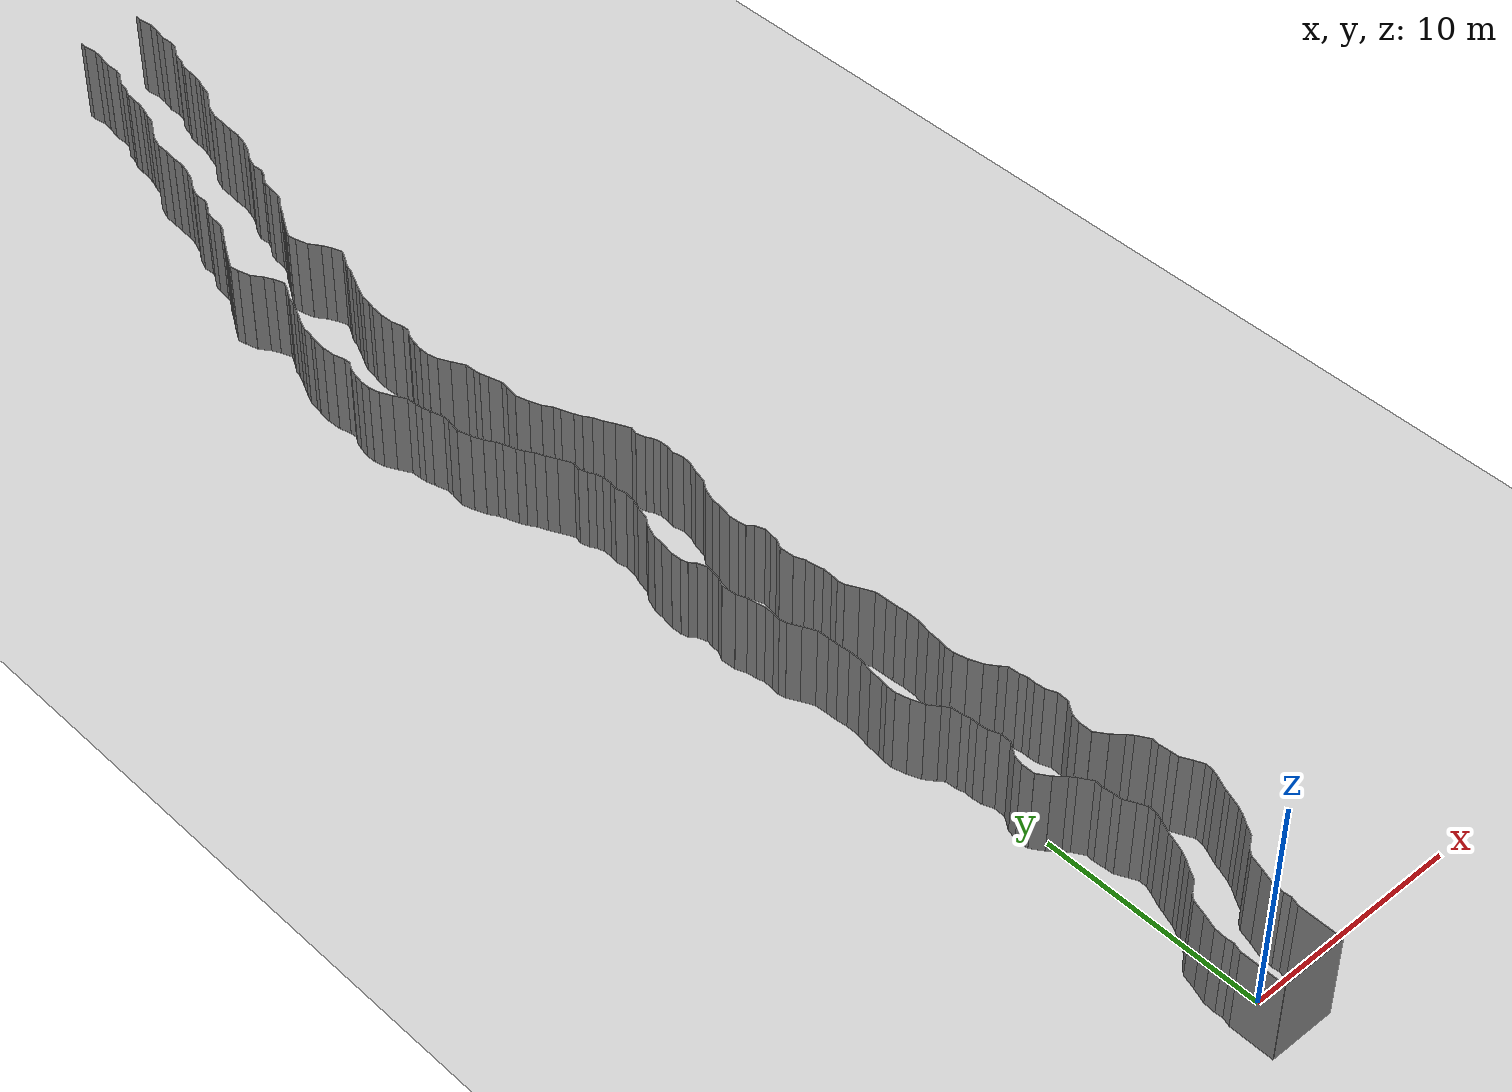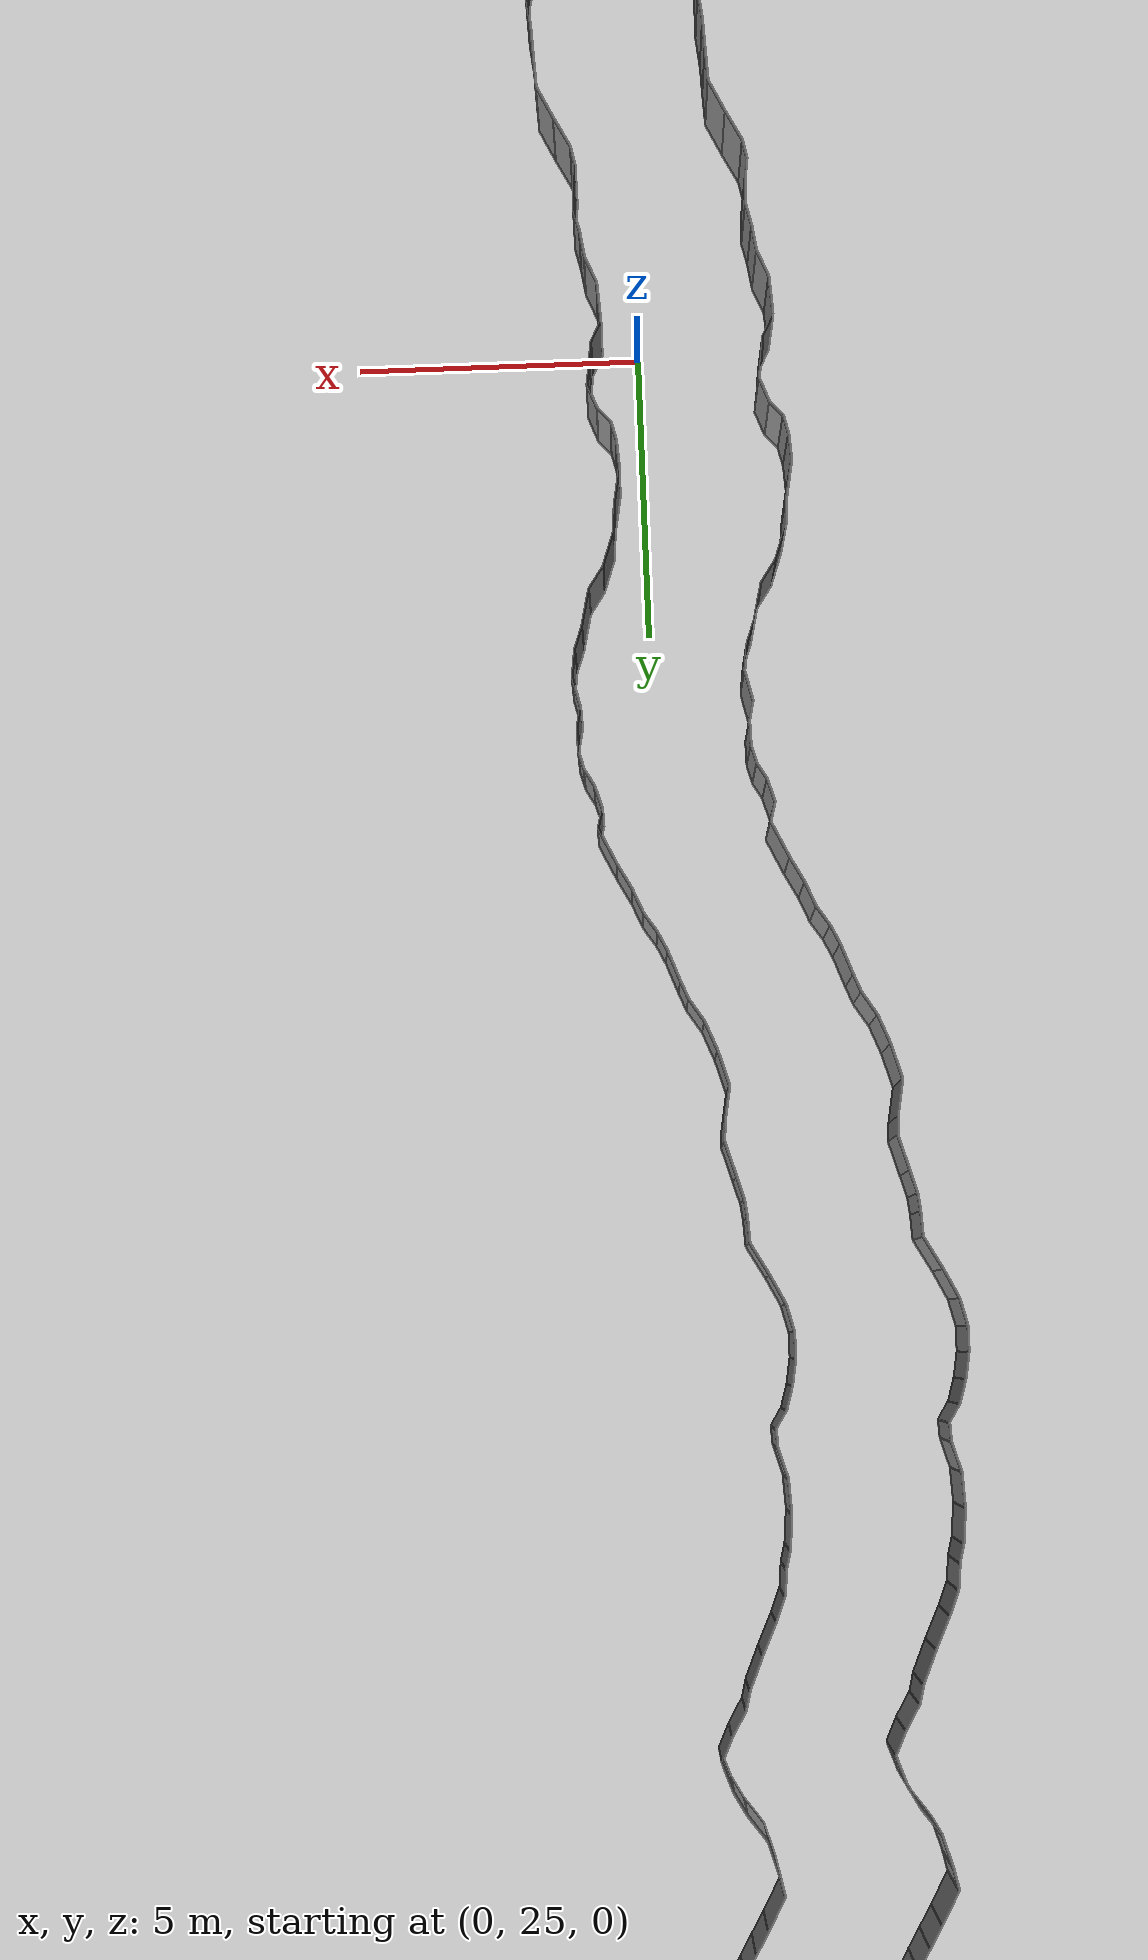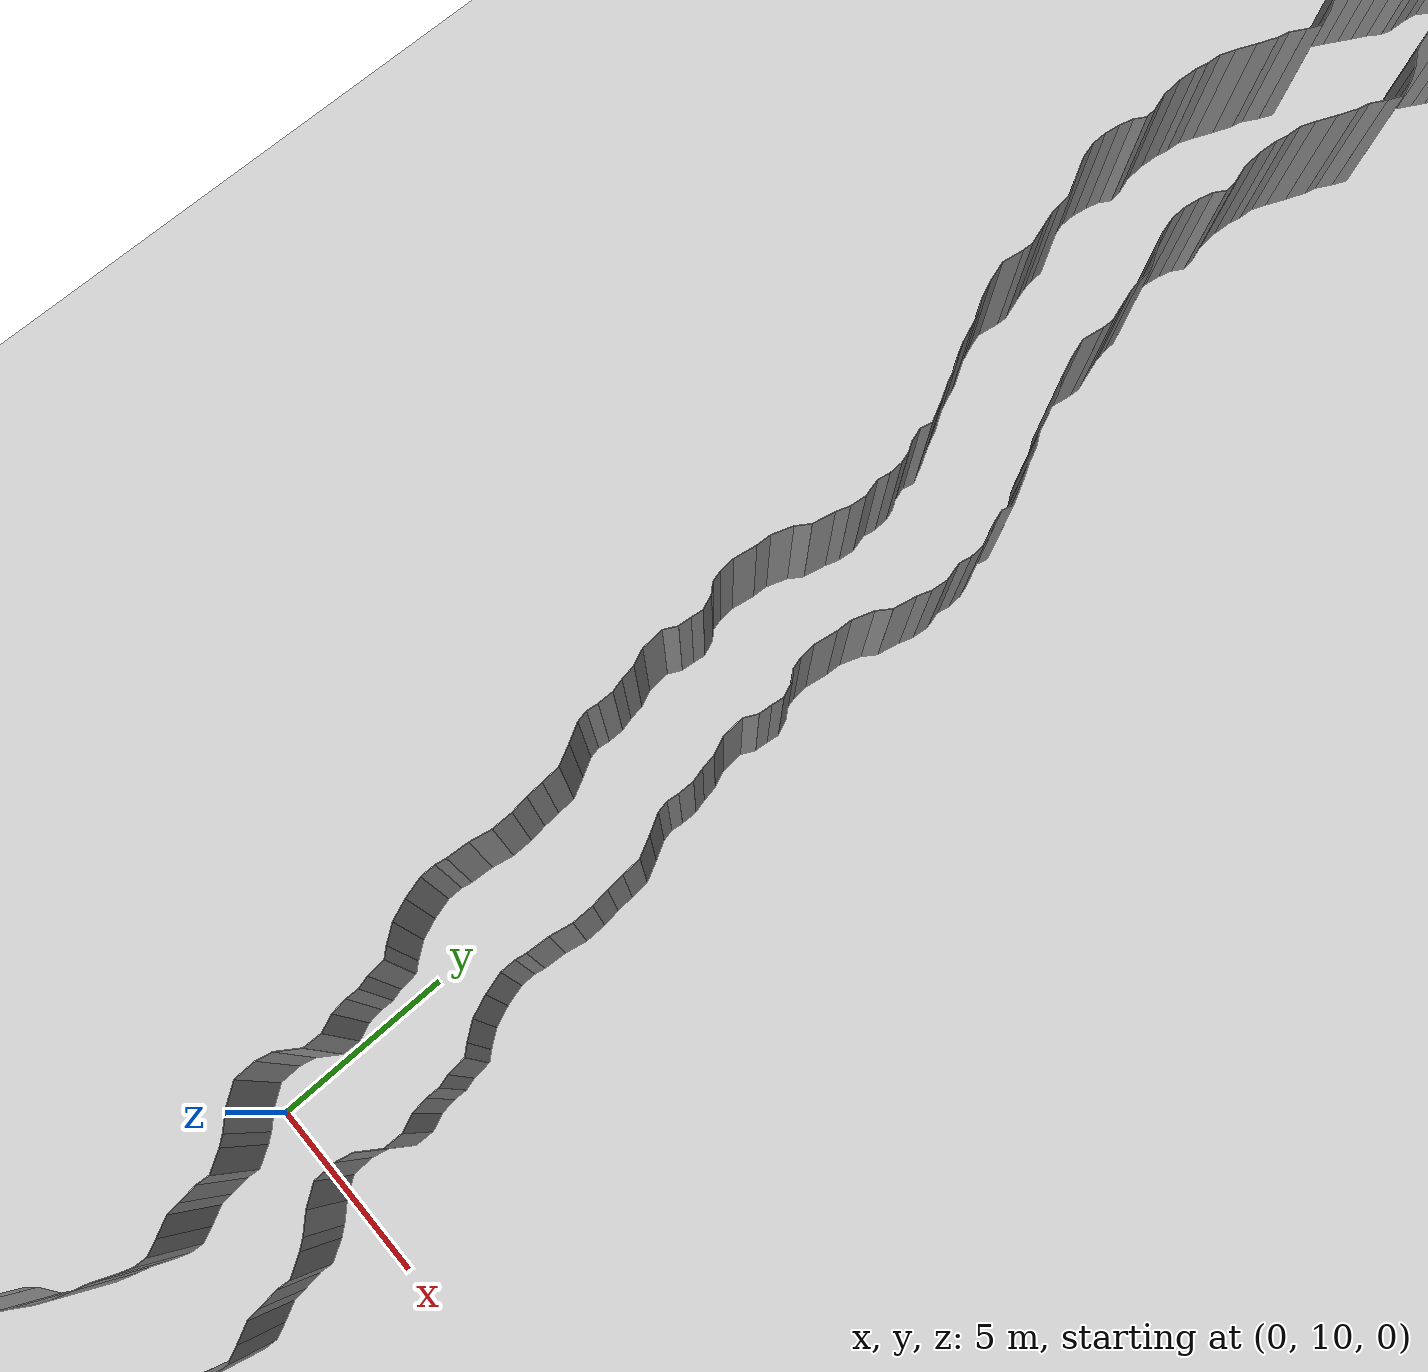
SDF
<sdf version="1.6">
 <world name="default">
  <light name="sun" type="directional">
   <pose>0 0 10 0 -0 0</pose>
   <diffuse>0.8 0.8 0.8 1</diffuse>
   <specular>0.2 0.2 0.2 1</specular>
   <attenuation>
    <range>1000</range>
    <constant>0.9</constant>
    <linear>0.01</linear>
    <quadratic>0.001</quadratic>
   </attenuation>
   <direction>-0.5 0.1 -0.9</direction>
  </light>
  <model name="ground_plane">
   <static>1</static>
   <link name="link">
    <collision name="collision">
     <geometry><plane><normal>0 0 1</normal><size>200 200</size></plane></geometry>
     <surface><friction><ode><mu>100</mu><mu2>50</mu2></ode></friction></surface>
    </collision>
    <visual name="visual">
     <cast_shadows>0</cast_shadows>
     <geometry><plane><normal>0 0 1</normal><size>200 200</size></plane></geometry>
     <material>
      <script><uri>file://media/materials/scripts/gazebo.material</uri><name>Gazebo/Grey</name></script>
     </material>
    </visual>
   </link>
   <pose>0 100 0 0 -0 0</pose>
  </model>
  <gravity>0 0 -9.8</gravity>
  <magnetic_field>6e-06 2.3e-05 -4.2e-05</magnetic_field>
  <atmosphere type="adiabatic"/>
  <physics default="0" name="default_physics" type="ode">
   <max_step_size>0.001</max_step_size>
   <real_time_factor>1</real_time_factor>
   <real_time_update_rate>1000</real_time_update_rate>
  </physics>
  <scene><ambient>0.4 0.4 0.4 1</ambient><background>0.7 0.7 0.7 1</background><shadows>1</shadows></scene>
  <spherical_coordinates>
   <surface_model>EARTH_WGS84</surface_model>
   <latitude_deg>0</latitude_deg>
   <longitude_deg>0</longitude_deg>
   <elevation>0</elevation>
   <heading_deg>0</heading_deg>
  </spherical_coordinates>
  <model name="wall_back">
   <static>1</static>
   <pose>0.0 -2 2 0.0 0 0.0</pose>
   <link name="link">
    <collision name="collision"><geometry><box><size>3 0.02 4</size></box></geometry></collision>
    <visual name="visual">
     <material>
      <script><name>Gazebo/Grey</name><uri>file://media/materials/scripts/gazebo.material</uri></script>
     </material>
     <geometry><box><size>3 0.02 4</size></box></geometry>
    </visual>
   </link>
  </model>
  <model name="wall_left">
   <static>1</static>
   <pose>1.5 -1 2 0 0 0.00</pose>
   <link name="link">
    <collision name="collision"><geometry><box><size>0.02 2 4</size></box></geometry></collision>
    <visual name="visual">
     <material>
      <script><name>Gazebo/Grey</name><uri>file://media/materials/scripts/gazebo.material</uri></script>
     </material>
     <geometry><box><size>0.02 2 4</size></box></geometry>
    </visual>
   </link>
  </model>
  <model name="wall_right">
   <static>1</static>
   <pose>-1.5 -1 2 0 0 0.00</pose>
   <link name="link">
    <collision name="collision"><geometry><box><size>0.02 2 4</size></box></geometry></collision>
    <visual name="visual">
     <material>
      <script><name>Gazebo/Grey</name><uri>file://media/materials/scripts/gazebo.material</uri></script>
     </material>
     <geometry><box><size>0.02 2 4</size></box></geometry>
    </visual>
   </link>
  </model>
  <model name="wall_0">
   <static>1</static>
   <pose>-1.437584540808723 0.19914146632163043 2 0 0 -0.30372527100131724</pose>
   <link name="link">
    <collision name="collision"><geometry><box><size>0.02 0.41738717352 4</size></box></geometry></collision>
    <visual name="visual">
     <material>
      <script><name>Gazebo/Grey</name><uri>file://media/materials/scripts/gazebo.material</uri></script>
     </material>
     <geometry><box><size>0.02 0.41738717352 4</size></box></geometry>
    </visual>
   </link>
  </model>
  <model name="wall_1">
   <static>1</static>
   <pose>1.562415459191277 0.19914146632163043 2 0 0 -0.30372527100131724</pose>
   <link name="link">
    <collision name="collision"><geometry><box><size>0.02 0.41738717352 4</size></box></geometry></collision>
    <visual name="visual">
     <material>
      <script><name>Gazebo/Grey</name><uri>file://media/materials/scripts/gazebo.material</uri></script>
     </material>
     <geometry><box><size>0.02 0.41738717352 4</size></box></geometry>
    </visual>
   </link>
  </model>
  <model name="wall_2">
   <static>1</static>
   <pose>-1.3948634828476751 0.5653040838758768 2 0 0 0.11737362302510895</pose>
   <link name="link">
    <collision name="collision"><geometry><box><size>0.02 0.336356563182 4</size></box></geometry></collision>
    <visual name="visual">
     <material>
      <script><name>Gazebo/Grey</name><uri>file://media/materials/scripts/gazebo.material</uri></script>
     </material>
     <geometry><box><size>0.02 0.336356563182 4</size></box></geometry>
    </visual>
   </link>
  </model>
  <model name="wall_3">
   <static>1</static>
   <pose>1.6051365171523249 0.5653040838758768 2 0 0 0.11737362302510895</pose>
   <link name="link">
    <collision name="collision"><geometry><box><size>0.02 0.336356563182 4</size></box></geometry></collision>
    <visual name="visual">
     <material>
      <script><name>Gazebo/Grey</name><uri>file://media/materials/scripts/gazebo.material</uri></script>
     </material>
     <geometry><box><size>0.02 0.336356563182 4</size></box></geometry>
    </visual>
   </link>
  </model>
  <model name="wall_4">
   <static>1</static>
   <pose>-1.394409642289166 1.0028298655659633 2 0 0 -0.0743466219727799</pose>
   <link name="link">
    <collision name="collision"><geometry><box><size>0.02 0.542507904997 4</size></box></geometry></collision>
    <visual name="visual">
     <material>
      <script><name>Gazebo/Grey</name><uri>file://media/materials/scripts/gazebo.material</uri></script>
     </material>
     <geometry><box><size>0.02 0.542507904997 4</size></box></geometry>
    </visual>
   </link>
  </model>
  <model name="wall_5">
   <static>1</static>
   <pose>1.605590357710834 1.0028298655659633 2 0 0 -0.0743466219727799</pose>
   <link name="link">
    <collision name="collision"><geometry><box><size>0.02 0.542507904997 4</size></box></geometry></collision>
    <visual name="visual">
     <material>
      <script><name>Gazebo/Grey</name><uri>file://media/materials/scripts/gazebo.material</uri></script>
     </material>
     <geometry><box><size>0.02 0.542507904997 4</size></box></geometry>
    </visual>
   </link>
  </model>
  <model name="wall_6">
   <static>1</static>
   <pose>-1.2648227173220237 1.6014009821625925 2 0 0 -0.3219787499781896</pose>
   <link name="link">
    <collision name="collision"><geometry><box><size>0.02 0.691677510704 4</size></box></geometry></collision>
    <visual name="visual">
     <material>
      <script><name>Gazebo/Grey</name><uri>file://media/materials/scripts/gazebo.material</uri></script>
     </material>
     <geometry><box><size>0.02 0.691677510704 4</size></box></geometry>
    </visual>
   </link>
  </model>
  <model name="wall_7">
   <static>1</static>
   <pose>1.7351772826779763 1.6014009821625925 2 0 0 -0.3219787499781896</pose>
   <link name="link">
    <collision name="collision"><geometry><box><size>0.02 0.691677510704 4</size></box></geometry></collision>
    <visual name="visual">
     <material>
      <script><name>Gazebo/Grey</name><uri>file://media/materials/scripts/gazebo.material</uri></script>
     </material>
     <geometry><box><size>0.02 0.691677510704 4</size></box></geometry>
    </visual>
   </link>
  </model>
  <model name="wall_8">
   <static>1</static>
   <pose>-1.0613258140084927 2.2554493884134152 2 0 0 -0.28090844949199845</pose>
   <link name="link">
    <collision name="collision"><geometry><box><size>0.02 0.678560715086 4</size></box></geometry></collision>
    <visual name="visual">
     <material>
      <script><name>Gazebo/Grey</name><uri>file://media/materials/scripts/gazebo.material</uri></script>
     </material>
     <geometry><box><size>0.02 0.678560715086 4</size></box></geometry>
    </visual>
   </link>
  </model>
  <model name="wall_9">
   <static>1</static>
   <pose>1.9386741859915073 2.2554493884134152 2 0 0 -0.28090844949199845</pose>
   <link name="link">
    <collision name="collision"><geometry><box><size>0.02 0.678560715086 4</size></box></geometry></collision>
    <visual name="visual">
     <material>
      <script><name>Gazebo/Grey</name><uri>file://media/materials/scripts/gazebo.material</uri></script>
     </material>
     <geometry><box><size>0.02 0.678560715086 4</size></box></geometry>
    </visual>
   </link>
  </model>
  <model name="wall_10">
   <static>1</static>
   <pose>-0.8550352063341324 2.713623595888301 2 0 0 -0.7039182181570224</pose>
   <link name="link">
    <collision name="collision"><geometry><box><size>0.02 0.346819316942 4</size></box></geometry></collision>
    <visual name="visual">
     <material>
      <script><name>Gazebo/Grey</name><uri>file://media/materials/scripts/gazebo.material</uri></script>
     </material>
     <geometry><box><size>0.02 0.346819316942 4</size></box></geometry>
    </visual>
   </link>
  </model>
  <model name="wall_11">
   <static>1</static>
   <pose>2.1449647936658676 2.713623595888301 2 0 0 -0.7039182181570224</pose>
   <link name="link">
    <collision name="collision"><geometry><box><size>0.02 0.346819316942 4</size></box></geometry></collision>
    <visual name="visual">
     <material>
      <script><name>Gazebo/Grey</name><uri>file://media/materials/scripts/gazebo.material</uri></script>
     </material>
     <geometry><box><size>0.02 0.346819316942 4</size></box></geometry>
    </visual>
   </link>
  </model>
  <model name="wall_12">
   <static>1</static>
   <pose>-0.49591066048191346 3.0213233668450896 2 0 0 -0.9528142580755041</pose>
   <link name="link">
    <collision name="collision"><geometry><box><size>0.02 0.605833688841 4</size></box></geometry></collision>
    <visual name="visual">
     <material>
      <script><name>Gazebo/Grey</name><uri>file://media/materials/scripts/gazebo.material</uri></script>
     </material>
     <geometry><box><size>0.02 0.605833688841 4</size></box></geometry>
    </visual>
   </link>
  </model>
  <model name="wall_13">
   <static>1</static>
   <pose>2.5040893395180865 3.0213233668450896 2 0 0 -0.9528142580755041</pose>
   <link name="link">
    <collision name="collision"><geometry><box><size>0.02 0.605833688841 4</size></box></geometry></collision>
    <visual name="visual">
     <material>
      <script><name>Gazebo/Grey</name><uri>file://media/materials/scripts/gazebo.material</uri></script>
     </material>
     <geometry><box><size>0.02 0.605833688841 4</size></box></geometry>
    </visual>
   </link>
  </model>
  <model name="wall_14">
   <static>1</static>
   <pose>-0.1232289149607314 3.4174996638244646 2 0 0 -0.5180971347103647</pose>
   <link name="link">
    <collision name="collision"><geometry><box><size>0.02 0.508006871808 4</size></box></geometry></collision>
    <visual name="visual">
     <material>
      <script><name>Gazebo/Grey</name><uri>file://media/materials/scripts/gazebo.material</uri></script>
     </material>
     <geometry><box><size>0.02 0.508006871808 4</size></box></geometry>
    </visual>
   </link>
  </model>
  <model name="wall_15">
   <static>1</static>
   <pose>2.8767710850392687 3.4174996638244646 2 0 0 -0.5180971347103647</pose>
   <link name="link">
    <collision name="collision"><geometry><box><size>0.02 0.508006871808 4</size></box></geometry></collision>
    <visual name="visual">
     <material>
      <script><name>Gazebo/Grey</name><uri>file://media/materials/scripts/gazebo.material</uri></script>
     </material>
     <geometry><box><size>0.02 0.508006871808 4</size></box></geometry>
    </visual>
   </link>
  </model>
  <model name="wall_16">
   <static>1</static>
   <pose>0.13868933347629092 3.8528305048694746 2 0 0 -0.5651544958231043</pose>
   <link name="link">
    <collision name="collision"><geometry><box><size>0.02 0.508373085545 4</size></box></geometry></collision>
    <visual name="visual">
     <material>
      <script><name>Gazebo/Grey</name><uri>file://media/materials/scripts/gazebo.material</uri></script>
     </material>
     <geometry><box><size>0.02 0.508373085545 4</size></box></geometry>
    </visual>
   </link>
  </model>
  <model name="wall_17">
   <static>1</static>
   <pose>3.138689333476291 3.8528305048694746 2 0 0 -0.5651544958231043</pose>
   <link name="link">
    <collision name="collision"><geometry><box><size>0.02 0.508373085545 4</size></box></geometry></collision>
    <visual name="visual">
     <material>
      <script><name>Gazebo/Grey</name><uri>file://media/materials/scripts/gazebo.material</uri></script>
     </material>
     <geometry><box><size>0.02 0.508373085545 4</size></box></geometry>
    </visual>
   </link>
  </model>
  <model name="wall_18">
   <static>1</static>
   <pose>0.3503488147982492 4.220972523937231 2 0 0 -0.4573250543680752</pose>
   <link name="link">
    <collision name="collision"><geometry><box><size>0.02 0.34211701242 4</size></box></geometry></collision>
    <visual name="visual">
     <material>
      <script><name>Gazebo/Grey</name><uri>file://media/materials/scripts/gazebo.material</uri></script>
     </material>
     <geometry><box><size>0.02 0.34211701242 4</size></box></geometry>
    </visual>
   </link>
  </model>
  <model name="wall_19">
   <static>1</static>
   <pose>3.350348814798249 4.220972523937231 2 0 0 -0.4573250543680752</pose>
   <link name="link">
    <collision name="collision"><geometry><box><size>0.02 0.34211701242 4</size></box></geometry></collision>
    <visual name="visual">
     <material>
      <script><name>Gazebo/Grey</name><uri>file://media/materials/scripts/gazebo.material</uri></script>
     </material>
     <geometry><box><size>0.02 0.34211701242 4</size></box></geometry>
    </visual>
   </link>
  </model>
  <model name="wall_20">
   <static>1</static>
   <pose>0.5238072433691114 4.657932478540906 2 0 0 -0.33261391376609967</pose>
   <link name="link">
    <collision name="collision"><geometry><box><size>0.02 0.599835664279 4</size></box></geometry></collision>
    <visual name="visual">
     <material>
      <script><name>Gazebo/Grey</name><uri>file://media/materials/scripts/gazebo.material</uri></script>
     </material>
     <geometry><box><size>0.02 0.599835664279 4</size></box></geometry>
    </visual>
   </link>
  </model>
  <model name="wall_21">
   <static>1</static>
   <pose>3.523807243369111 4.657932478540906 2 0 0 -0.33261391376609967</pose>
   <link name="link">
    <collision name="collision"><geometry><box><size>0.02 0.599835664279 4</size></box></geometry></collision>
    <visual name="visual">
     <material>
      <script><name>Gazebo/Grey</name><uri>file://media/materials/scripts/gazebo.material</uri></script>
     </material>
     <geometry><box><size>0.02 0.599835664279 4</size></box></geometry>
    </visual>
   </link>
  </model>
  <model name="wall_22">
   <static>1</static>
   <pose>0.6687756915646734 5.097011091971359 2 0 0 -0.29358537960156844</pose>
   <link name="link">
    <collision name="collision"><geometry><box><size>0.02 0.325107862448 4</size></box></geometry></collision>
    <visual name="visual">
     <material>
      <script><name>Gazebo/Grey</name><uri>file://media/materials/scripts/gazebo.material</uri></script>
     </material>
     <geometry><box><size>0.02 0.325107862448 4</size></box></geometry>
    </visual>
   </link>
  </model>
  <model name="wall_23">
   <static>1</static>
   <pose>3.668775691564673 5.097011091971359 2 0 0 -0.29358537960156844</pose>
   <link name="link">
    <collision name="collision"><geometry><box><size>0.02 0.325107862448 4</size></box></geometry></collision>
    <visual name="visual">
     <material>
      <script><name>Gazebo/Grey</name><uri>file://media/materials/scripts/gazebo.material</uri></script>
     </material>
     <geometry><box><size>0.02 0.325107862448 4</size></box></geometry>
    </visual>
   </link>
  </model>
  <model name="wall_24">
   <static>1</static>
   <pose>0.8478761278525622 5.553248437661183 2 0 0 -0.413889641027671</pose>
   <link name="link">
    <collision name="collision"><geometry><box><size>0.02 0.656729357501 4</size></box></geometry></collision>
    <visual name="visual">
     <material>
      <script><name>Gazebo/Grey</name><uri>file://media/materials/scripts/gazebo.material</uri></script>
     </material>
     <geometry><box><size>0.02 0.656729357501 4</size></box></geometry>
    </visual>
   </link>
  </model>
  <model name="wall_25">
   <static>1</static>
   <pose>3.847876127852562 5.553248437661183 2 0 0 -0.413889641027671</pose>
   <link name="link">
    <collision name="collision"><geometry><box><size>0.02 0.656729357501 4</size></box></geometry></collision>
    <visual name="visual">
     <material>
      <script><name>Gazebo/Grey</name><uri>file://media/materials/scripts/gazebo.material</uri></script>
     </material>
     <geometry><box><size>0.02 0.656729357501 4</size></box></geometry>
    </visual>
   </link>
  </model>
  <model name="wall_26">
   <static>1</static>
   <pose>1.0405157936755771 6.02449647832085 2 0 0 -0.3411937799384117</pose>
   <link name="link">
    <collision name="collision"><geometry><box><size>0.02 0.362091112633 4</size></box></geometry></collision>
    <visual name="visual">
     <material>
      <script><name>Gazebo/Grey</name><uri>file://media/materials/scripts/gazebo.material</uri></script>
     </material>
     <geometry><box><size>0.02 0.362091112633 4</size></box></geometry>
    </visual>
   </link>
  </model>
  <model name="wall_27">
   <static>1</static>
   <pose>4.040515793675577 6.02449647832085 2 0 0 -0.3411937799384117</pose>
   <link name="link">
    <collision name="collision"><geometry><box><size>0.02 0.362091112633 4</size></box></geometry></collision>
    <visual name="visual">
     <material>
      <script><name>Gazebo/Grey</name><uri>file://media/materials/scripts/gazebo.material</uri></script>
     </material>
     <geometry><box><size>0.02 0.362091112633 4</size></box></geometry>
    </visual>
   </link>
  </model>
  <model name="wall_28">
   <static>1</static>
   <pose>1.1144388519540367 6.371388264647776 2 0 0 -0.07554691758566276</pose>
   <link name="link">
    <collision name="collision"><geometry><box><size>0.02 0.353573383636 4</size></box></geometry></collision>
    <visual name="visual">
     <material>
      <script><name>Gazebo/Grey</name><uri>file://media/materials/scripts/gazebo.material</uri></script>
     </material>
     <geometry><box><size>0.02 0.353573383636 4</size></box></geometry>
    </visual>
   </link>
  </model>
  <model name="wall_29">
   <static>1</static>
   <pose>4.114438851954037 6.371388264647776 2 0 0 -0.07554691758566276</pose>
   <link name="link">
    <collision name="collision"><geometry><box><size>0.02 0.353573383636 4</size></box></geometry></collision>
    <visual name="visual">
     <material>
      <script><name>Gazebo/Grey</name><uri>file://media/materials/scripts/gazebo.material</uri></script>
     </material>
     <geometry><box><size>0.02 0.353573383636 4</size></box></geometry>
    </visual>
   </link>
  </model>
  <model name="wall_30">
   <static>1</static>
   <pose>1.033647632054986 6.745813201294141 2 0 0 0.4435163748197816</pose>
   <link name="link">
    <collision name="collision"><geometry><box><size>0.02 0.43873316639 4</size></box></geometry></collision>
    <visual name="visual">
     <material>
      <script><name>Gazebo/Grey</name><uri>file://media/materials/scripts/gazebo.material</uri></script>
     </material>
     <geometry><box><size>0.02 0.43873316639 4</size></box></geometry>
    </visual>
   </link>
  </model>
  <model name="wall_31">
   <static>1</static>
   <pose>4.033647632054986 6.745813201294141 2 0 0 0.4435163748197816</pose>
   <link name="link">
    <collision name="collision"><geometry><box><size>0.02 0.43873316639 4</size></box></geometry></collision>
    <visual name="visual">
     <material>
      <script><name>Gazebo/Grey</name><uri>file://media/materials/scripts/gazebo.material</uri></script>
     </material>
     <geometry><box><size>0.02 0.43873316639 4</size></box></geometry>
    </visual>
   </link>
  </model>
  <model name="wall_32">
   <static>1</static>
   <pose>0.8125762892889469 7.190634687882686 2 0 0 0.47524685223339913</pose>
   <link name="link">
    <collision name="collision"><geometry><box><size>0.02 0.554846142927 4</size></box></geometry></collision>
    <visual name="visual">
     <material>
      <script><name>Gazebo/Grey</name><uri>file://media/materials/scripts/gazebo.material</uri></script>
     </material>
     <geometry><box><size>0.02 0.554846142927 4</size></box></geometry>
    </visual>
   </link>
  </model>
  <model name="wall_33">
   <static>1</static>
   <pose>3.812576289288947 7.190634687882686 2 0 0 0.47524685223339913</pose>
   <link name="link">
    <collision name="collision"><geometry><box><size>0.02 0.554846142927 4</size></box></geometry></collision>
    <visual name="visual">
     <material>
      <script><name>Gazebo/Grey</name><uri>file://media/materials/scripts/gazebo.material</uri></script>
     </material>
     <geometry><box><size>0.02 0.554846142927 4</size></box></geometry>
    </visual>
   </link>
  </model>
  <model name="wall_34">
   <static>1</static>
   <pose>0.6719074328562987 7.618957834760673 2 0 0 0.07545331405848138</pose>
   <link name="link">
    <collision name="collision"><geometry><box><size>0.02 0.364324907448 4</size></box></geometry></collision>
    <visual name="visual">
     <material>
      <script><name>Gazebo/Grey</name><uri>file://media/materials/scripts/gazebo.material</uri></script>
     </material>
     <geometry><box><size>0.02 0.364324907448 4</size></box></geometry>
    </visual>
   </link>
  </model>
  <model name="wall_35">
   <static>1</static>
   <pose>3.671907432856299 7.618957834760673 2 0 0 0.07545331405848138</pose>
   <link name="link">
    <collision name="collision"><geometry><box><size>0.02 0.364324907448 4</size></box></geometry></collision>
    <visual name="visual">
     <material>
      <script><name>Gazebo/Grey</name><uri>file://media/materials/scripts/gazebo.material</uri></script>
     </material>
     <geometry><box><size>0.02 0.364324907448 4</size></box></geometry>
    </visual>
   </link>
  </model>
  <model name="wall_36">
   <static>1</static>
   <pose>0.6308984654413259 8.063215261044814 2 0 0 0.10349735906878753</pose>
   <link name="link">
    <collision name="collision"><geometry><box><size>0.02 0.528052186482 4</size></box></geometry></collision>
    <visual name="visual">
     <material>
      <script><name>Gazebo/Grey</name><uri>file://media/materials/scripts/gazebo.material</uri></script>
     </material>
     <geometry><box><size>0.02 0.528052186482 4</size></box></geometry>
    </visual>
   </link>
  </model>
  <model name="wall_37">
   <static>1</static>
   <pose>3.6308984654413257 8.063215261044814 2 0 0 0.10349735906878753</pose>
   <link name="link">
    <collision name="collision"><geometry><box><size>0.02 0.528052186482 4</size></box></geometry></collision>
    <visual name="visual">
     <material>
      <script><name>Gazebo/Grey</name><uri>file://media/materials/scripts/gazebo.material</uri></script>
     </material>
     <geometry><box><size>0.02 0.528052186482 4</size></box></geometry>
    </visual>
   </link>
  </model>
  <model name="wall_38">
   <static>1</static>
   <pose>0.6196103875067481 8.495250098855857 2 0 0 -0.09409633765073891</pose>
   <link name="link">
    <collision name="collision"><geometry><box><size>0.02 0.340348767814 4</size></box></geometry></collision>
    <visual name="visual">
     <material>
      <script><name>Gazebo/Grey</name><uri>file://media/materials/scripts/gazebo.material</uri></script>
     </material>
     <geometry><box><size>0.02 0.340348767814 4</size></box></geometry>
    </visual>
   </link>
  </model>
  <model name="wall_39">
   <static>1</static>
   <pose>3.6196103875067482 8.495250098855857 2 0 0 -0.09409633765073891</pose>
   <link name="link">
    <collision name="collision"><geometry><box><size>0.02 0.340348767814 4</size></box></geometry></collision>
    <visual name="visual">
     <material>
      <script><name>Gazebo/Grey</name><uri>file://media/materials/scripts/gazebo.material</uri></script>
     </material>
     <geometry><box><size>0.02 0.340348767814 4</size></box></geometry>
    </visual>
   </link>
  </model>
  <model name="wall_40">
   <static>1</static>
   <pose>0.4683702272360365 8.930815091683186 2 0 0 0.560999575177464</pose>
   <link name="link">
    <collision name="collision"><geometry><box><size>0.02 0.628642890016 4</size></box></geometry></collision>
    <visual name="visual">
     <material>
      <script><name>Gazebo/Grey</name><uri>file://media/materials/scripts/gazebo.material</uri></script>
     </material>
     <geometry><box><size>0.02 0.628642890016 4</size></box></geometry>
    </visual>
   </link>
  </model>
  <model name="wall_41">
   <static>1</static>
   <pose>3.4683702272360364 8.930815091683186 2 0 0 0.560999575177464</pose>
   <link name="link">
    <collision name="collision"><geometry><box><size>0.02 0.628642890016 4</size></box></geometry></collision>
    <visual name="visual">
     <material>
      <script><name>Gazebo/Grey</name><uri>file://media/materials/scripts/gazebo.material</uri></script>
     </material>
     <geometry><box><size>0.02 0.628642890016 4</size></box></geometry>
    </visual>
   </link>
  </model>
  <model name="wall_42">
   <static>1</static>
   <pose>0.20286799794410917 9.317444267156924 2 0 0 0.6842045653073365</pose>
   <link name="link">
    <collision name="collision"><geometry><box><size>0.02 0.310962243647 4</size></box></geometry></collision>
    <visual name="visual">
     <material>
      <script><name>Gazebo/Grey</name><uri>file://media/materials/scripts/gazebo.material</uri></script>
     </material>
     <geometry><box><size>0.02 0.310962243647 4</size></box></geometry>
    </visual>
   </link>
  </model>
  <model name="wall_43">
   <static>1</static>
   <pose>3.202867997944109 9.317444267156924 2 0 0 0.6842045653073365</pose>
   <link name="link">
    <collision name="collision"><geometry><box><size>0.02 0.310962243647 4</size></box></geometry></collision>
    <visual name="visual">
     <material>
      <script><name>Gazebo/Grey</name><uri>file://media/materials/scripts/gazebo.material</uri></script>
     </material>
     <geometry><box><size>0.02 0.310962243647 4</size></box></geometry>
    </visual>
   </link>
  </model>
  <model name="wall_44">
   <static>1</static>
   <pose>-0.10581616463823756 9.644450860844644 2 0 0 0.7947289484488541</pose>
   <link name="link">
    <collision name="collision"><geometry><box><size>0.02 0.589656704895 4</size></box></geometry></collision>
    <visual name="visual">
     <material>
      <script><name>Gazebo/Grey</name><uri>file://media/materials/scripts/gazebo.material</uri></script>
     </material>
     <geometry><box><size>0.02 0.589656704895 4</size></box></geometry>
    </visual>
   </link>
  </model>
  <model name="wall_45">
   <static>1</static>
   <pose>2.8941838353617624 9.644450860844644 2 0 0 0.7947289484488541</pose>
   <link name="link">
    <collision name="collision"><geometry><box><size>0.02 0.589656704895 4</size></box></geometry></collision>
    <visual name="visual">
     <material>
      <script><name>Gazebo/Grey</name><uri>file://media/materials/scripts/gazebo.material</uri></script>
     </material>
     <geometry><box><size>0.02 0.589656704895 4</size></box></geometry>
    </visual>
   </link>
  </model>
  <model name="wall_46">
   <static>1</static>
   <pose>-0.5037890396391627 10.109348792570279 2 0 0 0.6279122752231615</pose>
   <link name="link">
    <collision name="collision"><geometry><box><size>0.02 0.638554864892 4</size></box></geometry></collision>
    <visual name="visual">
     <material>
      <script><name>Gazebo/Grey</name><uri>file://media/materials/scripts/gazebo.material</uri></script>
     </material>
     <geometry><box><size>0.02 0.638554864892 4</size></box></geometry>
    </visual>
   </link>
  </model>
  <model name="wall_47">
   <static>1</static>
   <pose>2.4962109603608376 10.109348792570279 2 0 0 0.6279122752231615</pose>
   <link name="link">
    <collision name="collision"><geometry><box><size>0.02 0.638554864892 4</size></box></geometry></collision>
    <visual name="visual">
     <material>
      <script><name>Gazebo/Grey</name><uri>file://media/materials/scripts/gazebo.material</uri></script>
     </material>
     <geometry><box><size>0.02 0.638554864892 4</size></box></geometry>
    </visual>
   </link>
  </model>
  <model name="wall_48">
   <static>1</static>
   <pose>-0.6948387642877629 10.679753031650474 2 0 0 0.011178401615070197</pose>
   <link name="link">
    <collision name="collision"><geometry><box><size>0.02 0.624093294011 4</size></box></geometry></collision>
    <visual name="visual">
     <material>
      <script><name>Gazebo/Grey</name><uri>file://media/materials/scripts/gazebo.material</uri></script>
     </material>
     <geometry><box><size>0.02 0.624093294011 4</size></box></geometry>
    </visual>
   </link>
  </model>
  <model name="wall_49">
   <static>1</static>
   <pose>2.3051612357122373 10.679753031650474 2 0 0 0.011178401615070197</pose>
   <link name="link">
    <collision name="collision"><geometry><box><size>0.02 0.624093294011 4</size></box></geometry></collision>
    <visual name="visual">
     <material>
      <script><name>Gazebo/Grey</name><uri>file://media/materials/scripts/gazebo.material</uri></script>
     </material>
     <geometry><box><size>0.02 0.624093294011 4</size></box></geometry>
    </visual>
   </link>
  </model>
  <model name="wall_50">
   <static>1</static>
   <pose>-0.6452960002771193 11.209639009271081 2 0 0 -0.23877480551436756</pose>
   <link name="link">
    <collision name="collision"><geometry><box><size>0.02 0.448440595492 4</size></box></geometry></collision>
    <visual name="visual">
     <material>
      <script><name>Gazebo/Grey</name><uri>file://media/materials/scripts/gazebo.material</uri></script>
     </material>
     <geometry><box><size>0.02 0.448440595492 4</size></box></geometry>
    </visual>
   </link>
  </model>
  <model name="wall_51">
   <static>1</static>
   <pose>2.3547039997228807 11.209639009271081 2 0 0 -0.23877480551436756</pose>
   <link name="link">
    <collision name="collision"><geometry><box><size>0.02 0.448440595492 4</size></box></geometry></collision>
    <visual name="visual">
     <material>
      <script><name>Gazebo/Grey</name><uri>file://media/materials/scripts/gazebo.material</uri></script>
     </material>
     <geometry><box><size>0.02 0.448440595492 4</size></box></geometry>
    </visual>
   </link>
  </model>
  <model name="wall_52">
   <static>1</static>
   <pose>-0.3955156095086415 11.714015931435297 2 0 0 -0.6017380735763075</pose>
   <link name="link">
    <collision name="collision"><geometry><box><size>0.02 0.695134494645 4</size></box></geometry></collision>
    <visual name="visual">
     <material>
      <script><name>Gazebo/Grey</name><uri>file://media/materials/scripts/gazebo.material</uri></script>
     </material>
     <geometry><box><size>0.02 0.695134494645 4</size></box></geometry>
    </visual>
   </link>
  </model>
  <model name="wall_53">
   <static>1</static>
   <pose>2.6044843904913586 11.714015931435297 2 0 0 -0.6017380735763075</pose>
   <link name="link">
    <collision name="collision"><geometry><box><size>0.02 0.695134494645 4</size></box></geometry></collision>
    <visual name="visual">
     <material>
      <script><name>Gazebo/Grey</name><uri>file://media/materials/scripts/gazebo.material</uri></script>
     </material>
     <geometry><box><size>0.02 0.695134494645 4</size></box></geometry>
    </visual>
   </link>
  </model>
  <model name="wall_54">
   <static>1</static>
   <pose>-0.19075975531527672 12.260493217715691 2 0 0 -0.03078870763558765</pose>
   <link name="link">
    <collision name="collision"><geometry><box><size>0.02 0.520164905624 4</size></box></geometry></collision>
    <visual name="visual">
     <material>
      <script><name>Gazebo/Grey</name><uri>file://media/materials/scripts/gazebo.material</uri></script>
     </material>
     <geometry><box><size>0.02 0.520164905624 4</size></box></geometry>
    </visual>
   </link>
  </model>
  <model name="wall_55">
   <static>1</static>
   <pose>2.809240244684723 12.260493217715691 2 0 0 -0.03078870763558765</pose>
   <link name="link">
    <collision name="collision"><geometry><box><size>0.02 0.520164905624 4</size></box></geometry></collision>
    <visual name="visual">
     <material>
      <script><name>Gazebo/Grey</name><uri>file://media/materials/scripts/gazebo.material</uri></script>
     </material>
     <geometry><box><size>0.02 0.520164905624 4</size></box></geometry>
    </visual>
   </link>
  </model>
  <model name="wall_56">
   <static>1</static>
   <pose>-0.28001308719649437 12.752248717716782 2 0 0 0.39728035864173306</pose>
   <link name="link">
    <collision name="collision"><geometry><box><size>0.02 0.502748335885 4</size></box></geometry></collision>
    <visual name="visual">
     <material>
      <script><name>Gazebo/Grey</name><uri>file://media/materials/scripts/gazebo.material</uri></script>
     </material>
     <geometry><box><size>0.02 0.502748335885 4</size></box></geometry>
    </visual>
   </link>
  </model>
  <model name="wall_57">
   <static>1</static>
   <pose>2.7199869128035057 12.752248717716782 2 0 0 0.39728035864173306</pose>
   <link name="link">
    <collision name="collision"><geometry><box><size>0.02 0.502748335885 4</size></box></geometry></collision>
    <visual name="visual">
     <material>
      <script><name>Gazebo/Grey</name><uri>file://media/materials/scripts/gazebo.material</uri></script>
     </material>
     <geometry><box><size>0.02 0.502748335885 4</size></box></geometry>
    </visual>
   </link>
  </model>
  <model name="wall_58">
   <static>1</static>
   <pose>-0.40231754583288504 13.21279266981115 2 0 0 0.10905218262741671</pose>
   <link name="link">
    <collision name="collision"><geometry><box><size>0.02 0.460229184396 4</size></box></geometry></collision>
    <visual name="visual">
     <material>
      <script><name>Gazebo/Grey</name><uri>file://media/materials/scripts/gazebo.material</uri></script>
     </material>
     <geometry><box><size>0.02 0.460229184396 4</size></box></geometry>
    </visual>
   </link>
  </model>
  <model name="wall_59">
   <static>1</static>
   <pose>2.597682454167115 13.21279266981115 2 0 0 0.10905218262741671</pose>
   <link name="link">
    <collision name="collision"><geometry><box><size>0.02 0.460229184396 4</size></box></geometry></collision>
    <visual name="visual">
     <material>
      <script><name>Gazebo/Grey</name><uri>file://media/materials/scripts/gazebo.material</uri></script>
     </material>
     <geometry><box><size>0.02 0.460229184396 4</size></box></geometry>
    </visual>
   </link>
  </model>
  <model name="wall_60">
   <static>1</static>
   <pose>-0.4219806242729626 13.620806420169737 2 0 0 -0.030011779558620038</pose>
   <link name="link">
    <collision name="collision"><geometry><box><size>0.02 0.358693742009 4</size></box></geometry></collision>
    <visual name="visual">
     <material>
      <script><name>Gazebo/Grey</name><uri>file://media/materials/scripts/gazebo.material</uri></script>
     </material>
     <geometry><box><size>0.02 0.358693742009 4</size></box></geometry>
    </visual>
   </link>
  </model>
  <model name="wall_61">
   <static>1</static>
   <pose>2.5780193757270373 13.620806420169737 2 0 0 -0.030011779558620038</pose>
   <link name="link">
    <collision name="collision"><geometry><box><size>0.02 0.358693742009 4</size></box></geometry></collision>
    <visual name="visual">
     <material>
      <script><name>Gazebo/Grey</name><uri>file://media/materials/scripts/gazebo.material</uri></script>
     </material>
     <geometry><box><size>0.02 0.358693742009 4</size></box></geometry>
    </visual>
   </link>
  </model>
  <model name="wall_62">
   <static>1</static>
   <pose>-0.46280024762188854 13.97133946094752 2 0 0 0.2634901214733112</pose>
   <link name="link">
    <collision name="collision"><geometry><box><size>0.02 0.354778385369 4</size></box></geometry></collision>
    <visual name="visual">
     <material>
      <script><name>Gazebo/Grey</name><uri>file://media/materials/scripts/gazebo.material</uri></script>
     </material>
     <geometry><box><size>0.02 0.354778385369 4</size></box></geometry>
    </visual>
   </link>
  </model>
  <model name="wall_63">
   <static>1</static>
   <pose>2.5371997523781116 13.97133946094752 2 0 0 0.2634901214733112</pose>
   <link name="link">
    <collision name="collision"><geometry><box><size>0.02 0.354778385369 4</size></box></geometry></collision>
    <visual name="visual">
     <material>
      <script><name>Gazebo/Grey</name><uri>file://media/materials/scripts/gazebo.material</uri></script>
     </material>
     <geometry><box><size>0.02 0.354778385369 4</size></box></geometry>
    </visual>
   </link>
  </model>
  <model name="wall_64">
   <static>1</static>
   <pose>-0.531159644609888 14.405146660467546 2 0 0 0.08419917901794643</pose>
   <link name="link">
    <collision name="collision"><geometry><box><size>0.02 0.526947326369 4</size></box></geometry></collision>
    <visual name="visual">
     <material>
      <script><name>Gazebo/Grey</name><uri>file://media/materials/scripts/gazebo.material</uri></script>
     </material>
     <geometry><box><size>0.02 0.526947326369 4</size></box></geometry>
    </visual>
   </link>
  </model>
  <model name="wall_65">
   <static>1</static>
   <pose>2.468840355390112 14.405146660467546 2 0 0 0.08419917901794643</pose>
   <link name="link">
    <collision name="collision"><geometry><box><size>0.02 0.526947326369 4</size></box></geometry></collision>
    <visual name="visual">
     <material>
      <script><name>Gazebo/Grey</name><uri>file://media/materials/scripts/gazebo.material</uri></script>
     </material>
     <geometry><box><size>0.02 0.526947326369 4</size></box></geometry>
    </visual>
   </link>
  </model>
  <model name="wall_66">
   <static>1</static>
   <pose>-0.6654433372051671 14.791857538890236 2 0 0 0.7344681692740425</pose>
   <link name="link">
    <collision name="collision"><geometry><box><size>0.02 0.334607219005 4</size></box></geometry></collision>
    <visual name="visual">
     <material>
      <script><name>Gazebo/Grey</name><uri>file://media/materials/scripts/gazebo.material</uri></script>
     </material>
     <geometry><box><size>0.02 0.334607219005 4</size></box></geometry>
    </visual>
   </link>
  </model>
  <model name="wall_67">
   <static>1</static>
   <pose>2.334556662794833 14.791857538890236 2 0 0 0.7344681692740425</pose>
   <link name="link">
    <collision name="collision"><geometry><box><size>0.02 0.334607219005 4</size></box></geometry></collision>
    <visual name="visual">
     <material>
      <script><name>Gazebo/Grey</name><uri>file://media/materials/scripts/gazebo.material</uri></script>
     </material>
     <geometry><box><size>0.02 0.334607219005 4</size></box></geometry>
    </visual>
   </link>
  </model>
  <model name="wall_68">
   <static>1</static>
   <pose>-0.9462538041430467 15.141657639436584 2 0 0 0.6419753691294969</pose>
   <link name="link">
    <collision name="collision"><geometry><box><size>0.02 0.563429641958 4</size></box></geometry></collision>
    <visual name="visual">
     <material>
      <script><name>Gazebo/Grey</name><uri>file://media/materials/scripts/gazebo.material</uri></script>
     </material>
     <geometry><box><size>0.02 0.563429641958 4</size></box></geometry>
    </visual>
   </link>
  </model>
  <model name="wall_69">
   <static>1</static>
   <pose>2.053746195856953 15.141657639436584 2 0 0 0.6419753691294969</pose>
   <link name="link">
    <collision name="collision"><geometry><box><size>0.02 0.563429641958 4</size></box></geometry></collision>
    <visual name="visual">
     <material>
      <script><name>Gazebo/Grey</name><uri>file://media/materials/scripts/gazebo.material</uri></script>
     </material>
     <geometry><box><size>0.02 0.563429641958 4</size></box></geometry>
    </visual>
   </link>
  </model>
  <model name="wall_70">
   <static>1</static>
   <pose>-1.2304791952523164 15.65304504788151 2 0 0 0.3842337161596434</pose>
   <link name="link">
    <collision name="collision"><geometry><box><size>0.02 0.616464787114 4</size></box></geometry></collision>
    <visual name="visual">
     <material>
      <script><name>Gazebo/Grey</name><uri>file://media/materials/scripts/gazebo.material</uri></script>
     </material>
     <geometry><box><size>0.02 0.616464787114 4</size></box></geometry>
    </visual>
   </link>
  </model>
  <model name="wall_71">
   <static>1</static>
   <pose>1.7695208047476836 15.65304504788151 2 0 0 0.3842337161596434</pose>
   <link name="link">
    <collision name="collision"><geometry><box><size>0.02 0.616464787114 4</size></box></geometry></collision>
    <visual name="visual">
     <material>
      <script><name>Gazebo/Grey</name><uri>file://media/materials/scripts/gazebo.material</uri></script>
     </material>
     <geometry><box><size>0.02 0.616464787114 4</size></box></geometry>
    </visual>
   </link>
  </model>
  <model name="wall_72">
   <static>1</static>
   <pose>-1.4282986551377834 16.238100182832095 2 0 0 0.2682797676968485</pose>
   <link name="link">
    <collision name="collision"><geometry><box><size>0.02 0.620801550412 4</size></box></geometry></collision>
    <visual name="visual">
     <material>
      <script><name>Gazebo/Grey</name><uri>file://media/materials/scripts/gazebo.material</uri></script>
     </material>
     <geometry><box><size>0.02 0.620801550412 4</size></box></geometry>
    </visual>
   </link>
  </model>
  <model name="wall_73">
   <static>1</static>
   <pose>1.5717013448622166 16.238100182832095 2 0 0 0.2682797676968485</pose>
   <link name="link">
    <collision name="collision"><geometry><box><size>0.02 0.620801550412 4</size></box></geometry></collision>
    <visual name="visual">
     <material>
      <script><name>Gazebo/Grey</name><uri>file://media/materials/scripts/gazebo.material</uri></script>
     </material>
     <geometry><box><size>0.02 0.620801550412 4</size></box></geometry>
    </visual>
   </link>
  </model>
  <model name="wall_74">
   <static>1</static>
   <pose>-1.50974459134682 16.75761538846065 2 0 0 -0.0037824602446166916</pose>
   <link name="link">
    <collision name="collision"><geometry><box><size>0.02 0.440439132026 4</size></box></geometry></collision>
    <visual name="visual">
     <material>
      <script><name>Gazebo/Grey</name><uri>file://media/materials/scripts/gazebo.material</uri></script>
     </material>
     <geometry><box><size>0.02 0.440439132026 4</size></box></geometry>
    </visual>
   </link>
  </model>
  <model name="wall_75">
   <static>1</static>
   <pose>1.49025540865318 16.75761538846065 2 0 0 -0.0037824602446166916</pose>
   <link name="link">
    <collision name="collision"><geometry><box><size>0.02 0.440439132026 4</size></box></geometry></collision>
    <visual name="visual">
     <material>
      <script><name>Gazebo/Grey</name><uri>file://media/materials/scripts/gazebo.material</uri></script>
     </material>
     <geometry><box><size>0.02 0.440439132026 4</size></box></geometry>
    </visual>
   </link>
  </model>
  <model name="wall_76">
   <static>1</static>
   <pose>-1.4788715510664707 17.12615217923091 2 0 0 -0.19983395495206277</pose>
   <link name="link">
    <collision name="collision"><geometry><box><size>0.02 0.302660683265 4</size></box></geometry></collision>
    <visual name="visual">
     <material>
      <script><name>Gazebo/Grey</name><uri>file://media/materials/scripts/gazebo.material</uri></script>
     </material>
     <geometry><box><size>0.02 0.302660683265 4</size></box></geometry>
    </visual>
   </link>
  </model>
  <model name="wall_77">
   <static>1</static>
   <pose>1.5211284489335293 17.12615217923091 2 0 0 -0.19983395495206277</pose>
   <link name="link">
    <collision name="collision"><geometry><box><size>0.02 0.302660683265 4</size></box></geometry></collision>
    <visual name="visual">
     <material>
      <script><name>Gazebo/Grey</name><uri>file://media/materials/scripts/gazebo.material</uri></script>
     </material>
     <geometry><box><size>0.02 0.302660683265 4</size></box></geometry>
    </visual>
   </link>
  </model>
  <model name="wall_78">
   <static>1</static>
   <pose>-1.4244664659801647 17.600824211612792 2 0 0 -0.07452016327790473</pose>
   <link name="link">
    <collision name="collision"><geometry><box><size>0.02 0.654522990148 4</size></box></geometry></collision>
    <visual name="visual">
     <material>
      <script><name>Gazebo/Grey</name><uri>file://media/materials/scripts/gazebo.material</uri></script>
     </material>
     <geometry><box><size>0.02 0.654522990148 4</size></box></geometry>
    </visual>
   </link>
  </model>
  <model name="wall_79">
   <static>1</static>
   <pose>1.5755335340198353 17.600824211612792 2 0 0 -0.07452016327790473</pose>
   <link name="link">
    <collision name="collision"><geometry><box><size>0.02 0.654522990148 4</size></box></geometry></collision>
    <visual name="visual">
     <material>
      <script><name>Gazebo/Grey</name><uri>file://media/materials/scripts/gazebo.material</uri></script>
     </material>
     <geometry><box><size>0.02 0.654522990148 4</size></box></geometry>
    </visual>
   </link>
  </model>
  <model name="wall_80">
   <static>1</static>
   <pose>-1.3352252308877155 18.236211478110285 2 0 0 -0.20692733711803735</pose>
   <link name="link">
    <collision name="collision"><geometry><box><size>0.02 0.631540840454 4</size></box></geometry></collision>
    <visual name="visual">
     <material>
      <script><name>Gazebo/Grey</name><uri>file://media/materials/scripts/gazebo.material</uri></script>
     </material>
     <geometry><box><size>0.02 0.631540840454 4</size></box></geometry>
    </visual>
   </link>
  </model>
  <model name="wall_81">
   <static>1</static>
   <pose>1.6647747691122845 18.236211478110285 2 0 0 -0.20692733711803735</pose>
   <link name="link">
    <collision name="collision"><geometry><box><size>0.02 0.631540840454 4</size></box></geometry></collision>
    <visual name="visual">
     <material>
      <script><name>Gazebo/Grey</name><uri>file://media/materials/scripts/gazebo.material</uri></script>
     </material>
     <geometry><box><size>0.02 0.631540840454 4</size></box></geometry>
    </visual>
   </link>
  </model>
  <model name="wall_82">
   <static>1</static>
   <pose>-1.2701465992344358 18.85010995103074 2 0 0 -0.0006639380611708689</pose>
   <link name="link">
    <collision name="collision"><geometry><box><size>0.02 0.609729011805 4</size></box></geometry></collision>
    <visual name="visual">
     <material>
      <script><name>Gazebo/Grey</name><uri>file://media/materials/scripts/gazebo.material</uri></script>
     </material>
     <geometry><box><size>0.02 0.609729011805 4</size></box></geometry>
    </visual>
   </link>
  </model>
  <model name="wall_83">
   <static>1</static>
   <pose>1.7298534007655642 18.85010995103074 2 0 0 -0.0006639380611708689</pose>
   <link name="link">
    <collision name="collision"><geometry><box><size>0.02 0.609729011805 4</size></box></geometry></collision>
    <visual name="visual">
     <material>
      <script><name>Gazebo/Grey</name><uri>file://media/materials/scripts/gazebo.material</uri></script>
     </material>
     <geometry><box><size>0.02 0.609729011805 4</size></box></geometry>
    </visual>
   </link>
  </model>
  <model name="wall_84">
   <static>1</static>
   <pose>-1.299373359090749 19.41177049488187 2 0 0 0.11410352644146506</pose>
   <link name="link">
    <collision name="collision"><geometry><box><size>0.02 0.516953830518 4</size></box></geometry></collision>
    <visual name="visual">
     <material>
      <script><name>Gazebo/Grey</name><uri>file://media/materials/scripts/gazebo.material</uri></script>
     </material>
     <geometry><box><size>0.02 0.516953830518 4</size></box></geometry>
    </visual>
   </link>
  </model>
  <model name="wall_85">
   <static>1</static>
   <pose>1.700626640909251 19.41177049488187 2 0 0 0.11410352644146506</pose>
   <link name="link">
    <collision name="collision"><geometry><box><size>0.02 0.516953830518 4</size></box></geometry></collision>
    <visual name="visual">
     <material>
      <script><name>Gazebo/Grey</name><uri>file://media/materials/scripts/gazebo.material</uri></script>
     </material>
     <geometry><box><size>0.02 0.516953830518 4</size></box></geometry>
    </visual>
   </link>
  </model>
  <model name="wall_86">
   <static>1</static>
   <pose>-1.3411813555637073 19.92039152996001 2 0 0 0.04911693752746528</pose>
   <link name="link">
    <collision name="collision"><geometry><box><size>0.02 0.504257992132 4</size></box></geometry></collision>
    <visual name="visual">
     <material>
      <script><name>Gazebo/Grey</name><uri>file://media/materials/scripts/gazebo.material</uri></script>
     </material>
     <geometry><box><size>0.02 0.504257992132 4</size></box></geometry>
    </visual>
   </link>
  </model>
  <model name="wall_87">
   <static>1</static>
   <pose>1.6588186444362927 19.92039152996001 2 0 0 0.04911693752746528</pose>
   <link name="link">
    <collision name="collision"><geometry><box><size>0.02 0.504257992132 4</size></box></geometry></collision>
    <visual name="visual">
     <material>
      <script><name>Gazebo/Grey</name><uri>file://media/materials/scripts/gazebo.material</uri></script>
     </material>
     <geometry><box><size>0.02 0.504257992132 4</size></box></geometry>
    </visual>
   </link>
  </model>
  <model name="wall_88">
   <static>1</static>
   <pose>-1.3693698605942195 20.44796934330465 2 0 0 0.05727008561438874</pose>
   <link name="link">
    <collision name="collision"><geometry><box><size>0.02 0.552411436073 4</size></box></geometry></collision>
    <visual name="visual">
     <material>
      <script><name>Gazebo/Grey</name><uri>file://media/materials/scripts/gazebo.material</uri></script>
     </material>
     <geometry><box><size>0.02 0.552411436073 4</size></box></geometry>
    </visual>
   </link>
  </model>
  <model name="wall_89">
   <static>1</static>
   <pose>1.6306301394057805 20.44796934330465 2 0 0 0.05727008561438874</pose>
   <link name="link">
    <collision name="collision"><geometry><box><size>0.02 0.552411436073 4</size></box></geometry></collision>
    <visual name="visual">
     <material>
      <script><name>Gazebo/Grey</name><uri>file://media/materials/scripts/gazebo.material</uri></script>
     </material>
     <geometry><box><size>0.02 0.552411436073 4</size></box></geometry>
    </visual>
   </link>
  </model>
  <model name="wall_90">
   <static>1</static>
   <pose>-1.5231800420298953 20.999573042570326 2 0 0 0.46386536665233824</pose>
   <link name="link">
    <collision name="collision"><geometry><box><size>0.02 0.616888356608 4</size></box></geometry></collision>
    <visual name="visual">
     <material>
      <script><name>Gazebo/Grey</name><uri>file://media/materials/scripts/gazebo.material</uri></script>
     </material>
     <geometry><box><size>0.02 0.616888356608 4</size></box></geometry>
    </visual>
   </link>
  </model>
  <model name="wall_91">
   <static>1</static>
   <pose>1.4768199579701047 20.999573042570326 2 0 0 0.46386536665233824</pose>
   <link name="link">
    <collision name="collision"><geometry><box><size>0.02 0.616888356608 4</size></box></geometry></collision>
    <visual name="visual">
     <material>
      <script><name>Gazebo/Grey</name><uri>file://media/materials/scripts/gazebo.material</uri></script>
     </material>
     <geometry><box><size>0.02 0.616888356608 4</size></box></geometry>
    </visual>
   </link>
  </model>
  <model name="wall_92">
   <static>1</static>
   <pose>-1.8007864723309284 21.532290220596444 2 0 0 0.49783629137514196</pose>
   <link name="link">
    <collision name="collision"><geometry><box><size>0.02 0.584705543885 4</size></box></geometry></collision>
    <visual name="visual">
     <material>
      <script><name>Gazebo/Grey</name><uri>file://media/materials/scripts/gazebo.material</uri></script>
     </material>
     <geometry><box><size>0.02 0.584705543885 4</size></box></geometry>
    </visual>
   </link>
  </model>
  <model name="wall_93">
   <static>1</static>
   <pose>1.1992135276690716 21.532290220596444 2 0 0 0.49783629137514196</pose>
   <link name="link">
    <collision name="collision"><geometry><box><size>0.02 0.584705543885 4</size></box></geometry></collision>
    <visual name="visual">
     <material>
      <script><name>Gazebo/Grey</name><uri>file://media/materials/scripts/gazebo.material</uri></script>
     </material>
     <geometry><box><size>0.02 0.584705543885 4</size></box></geometry>
    </visual>
   </link>
  </model>
  <model name="wall_94">
   <static>1</static>
   <pose>-1.9741265558823107 21.956182674335075 2 0 0 0.19928846943864703</pose>
   <link name="link">
    <collision name="collision"><geometry><box><size>0.02 0.340797350269 4</size></box></geometry></collision>
    <visual name="visual">
     <material>
      <script><name>Gazebo/Grey</name><uri>file://media/materials/scripts/gazebo.material</uri></script>
     </material>
     <geometry><box><size>0.02 0.340797350269 4</size></box></geometry>
    </visual>
   </link>
  </model>
  <model name="wall_95">
   <static>1</static>
   <pose>1.0258734441176893 21.956182674335075 2 0 0 0.19928846943864703</pose>
   <link name="link">
    <collision name="collision"><geometry><box><size>0.02 0.340797350269 4</size></box></geometry></collision>
    <visual name="visual">
     <material>
      <script><name>Gazebo/Grey</name><uri>file://media/materials/scripts/gazebo.material</uri></script>
     </material>
     <geometry><box><size>0.02 0.340797350269 4</size></box></geometry>
    </visual>
   </link>
  </model>
  <model name="wall_96">
   <static>1</static>
   <pose>-1.9852331832228716 22.29065924674199 2 0 0 -0.13431607236533805</pose>
   <link name="link">
    <collision name="collision"><geometry><box><size>0.02 0.337944779792 4</size></box></geometry></collision>
    <visual name="visual">
     <material>
      <script><name>Gazebo/Grey</name><uri>file://media/materials/scripts/gazebo.material</uri></script>
     </material>
     <geometry><box><size>0.02 0.337944779792 4</size></box></geometry>
    </visual>
   </link>
  </model>
  <model name="wall_97">
   <static>1</static>
   <pose>1.0147668167771284 22.29065924674199 2 0 0 -0.13431607236533805</pose>
   <link name="link">
    <collision name="collision"><geometry><box><size>0.02 0.337944779792 4</size></box></geometry></collision>
    <visual name="visual">
     <material>
      <script><name>Gazebo/Grey</name><uri>file://media/materials/scripts/gazebo.material</uri></script>
     </material>
     <geometry><box><size>0.02 0.337944779792 4</size></box></geometry>
    </visual>
   </link>
  </model>
  <model name="wall_98">
   <static>1</static>
   <pose>-1.957455391450274 22.690313694674614 2 0 0 -0.022176277751504197</pose>
   <link name="link">
    <collision name="collision"><geometry><box><size>0.02 0.464522152554 4</size></box></geometry></collision>
    <visual name="visual">
     <material>
      <script><name>Gazebo/Grey</name><uri>file://media/materials/scripts/gazebo.material</uri></script>
     </material>
     <geometry><box><size>0.02 0.464522152554 4</size></box></geometry>
    </visual>
   </link>
  </model>
  <model name="wall_99">
   <static>1</static>
   <pose>1.042544608549726 22.690313694674614 2 0 0 -0.022176277751504197</pose>
   <link name="link">
    <collision name="collision"><geometry><box><size>0.02 0.464522152554 4</size></box></geometry></collision>
    <visual name="visual">
     <material>
      <script><name>Gazebo/Grey</name><uri>file://media/materials/scripts/gazebo.material</uri></script>
     </material>
     <geometry><box><size>0.02 0.464522152554 4</size></box></geometry>
    </visual>
   </link>
  </model>
  <model name="wall_100">
   <static>1</static>
   <pose>-1.9981191306679005 23.109032375694895 2 0 0 0.24086350407893845</pose>
   <link name="link">
    <collision name="collision"><geometry><box><size>0.02 0.384118009989 4</size></box></geometry></collision>
    <visual name="visual">
     <material>
      <script><name>Gazebo/Grey</name><uri>file://media/materials/scripts/gazebo.material</uri></script>
     </material>
     <geometry><box><size>0.02 0.384118009989 4</size></box></geometry>
    </visual>
   </link>
  </model>
  <model name="wall_101">
   <static>1</static>
   <pose>1.0018808693320995 23.109032375694895 2 0 0 0.24086350407893845</pose>
   <link name="link">
    <collision name="collision"><geometry><box><size>0.02 0.384118009989 4</size></box></geometry></collision>
    <visual name="visual">
     <material>
      <script><name>Gazebo/Grey</name><uri>file://media/materials/scripts/gazebo.material</uri></script>
     </material>
     <geometry><box><size>0.02 0.384118009989 4</size></box></geometry>
    </visual>
   </link>
  </model>
  <model name="wall_102">
   <static>1</static>
   <pose>-2.0779140029207506 23.517107589674563 2 0 0 0.15218474667878146</pose>
   <link name="link">
    <collision name="collision"><geometry><box><size>0.02 0.448302374056 4</size></box></geometry></collision>
    <visual name="visual">
     <material>
      <script><name>Gazebo/Grey</name><uri>file://media/materials/scripts/gazebo.material</uri></script>
     </material>
     <geometry><box><size>0.02 0.448302374056 4</size></box></geometry>
    </visual>
   </link>
  </model>
  <model name="wall_103">
   <static>1</static>
   <pose>0.9220859970792494 23.517107589674563 2 0 0 0.15218474667878146</pose>
   <link name="link">
    <collision name="collision"><geometry><box><size>0.02 0.448302374056 4</size></box></geometry></collision>
    <visual name="visual">
     <material>
      <script><name>Gazebo/Grey</name><uri>file://media/materials/scripts/gazebo.material</uri></script>
     </material>
     <geometry><box><size>0.02 0.448302374056 4</size></box></geometry>
    </visual>
   </link>
  </model>
  <model name="wall_104">
   <static>1</static>
   <pose>-2.2093518582087603 23.965898470175 2 0 0 0.4051614446278775</pose>
   <link name="link">
    <collision name="collision"><geometry><box><size>0.02 0.494495743005 4</size></box></geometry></collision>
    <visual name="visual">
     <material>
      <script><name>Gazebo/Grey</name><uri>file://media/materials/scripts/gazebo.material</uri></script>
     </material>
     <geometry><box><size>0.02 0.494495743005 4</size></box></geometry>
    </visual>
   </link>
  </model>
  <model name="wall_105">
   <static>1</static>
   <pose>0.7906481417912397 23.965898470175 2 0 0 0.4051614446278775</pose>
   <link name="link">
    <collision name="collision"><geometry><box><size>0.02 0.494495743005 4</size></box></geometry></collision>
    <visual name="visual">
     <material>
      <script><name>Gazebo/Grey</name><uri>file://media/materials/scripts/gazebo.material</uri></script>
     </material>
     <geometry><box><size>0.02 0.494495743005 4</size></box></geometry>
    </visual>
   </link>
  </model>
  <model name="wall_106">
   <static>1</static>
   <pose>-2.3298995162277705 24.53259080262013 2 0 0 0.06791676471023138</pose>
   <link name="link">
    <collision name="collision"><geometry><box><size>0.02 0.680492750816 4</size></box></geometry></collision>
    <visual name="visual">
     <material>
      <script><name>Gazebo/Grey</name><uri>file://media/materials/scripts/gazebo.material</uri></script>
     </material>
     <geometry><box><size>0.02 0.680492750816 4</size></box></geometry>
    </visual>
   </link>
  </model>
  <model name="wall_107">
   <static>1</static>
   <pose>0.6701004837722295 24.53259080262013 2 0 0 0.06791676471023138</pose>
   <link name="link">
    <collision name="collision"><geometry><box><size>0.02 0.680492750816 4</size></box></geometry></collision>
    <visual name="visual">
     <material>
      <script><name>Gazebo/Grey</name><uri>file://media/materials/scripts/gazebo.material</uri></script>
     </material>
     <geometry><box><size>0.02 0.680492750816 4</size></box></geometry>
    </visual>
   </link>
  </model>
  <model name="wall_108">
   <static>1</static>
   <pose>-2.2571940620833413 25.058265987990737 2 0 0 -0.4751352688544091</pose>
   <link name="link">
    <collision name="collision"><geometry><box><size>0.02 0.418818653009 4</size></box></geometry></collision>
    <visual name="visual">
     <material>
      <script><name>Gazebo/Grey</name><uri>file://media/materials/scripts/gazebo.material</uri></script>
     </material>
     <geometry><box><size>0.02 0.418818653009 4</size></box></geometry>
    </visual>
   </link>
  </model>
  <model name="wall_109">
   <static>1</static>
   <pose>0.7428059379166587 25.058265987990737 2 0 0 -0.4751352688544091</pose>
   <link name="link">
    <collision name="collision"><geometry><box><size>0.02 0.418818653009 4</size></box></geometry></collision>
    <visual name="visual">
     <material>
      <script><name>Gazebo/Grey</name><uri>file://media/materials/scripts/gazebo.material</uri></script>
     </material>
     <geometry><box><size>0.02 0.418818653009 4</size></box></geometry>
    </visual>
   </link>
  </model>
  <model name="wall_110">
   <static>1</static>
   <pose>-2.1412712356360597 25.433382794964054 2 0 0 -0.10614440251509129</pose>
   <link name="link">
    <collision name="collision"><geometry><box><size>0.02 0.379945491842 4</size></box></geometry></collision>
    <visual name="visual">
     <material>
      <script><name>Gazebo/Grey</name><uri>file://media/materials/scripts/gazebo.material</uri></script>
     </material>
     <geometry><box><size>0.02 0.379945491842 4</size></box></geometry>
    </visual>
   </link>
  </model>
  <model name="wall_111">
   <static>1</static>
   <pose>0.8587287643639403 25.433382794964054 2 0 0 -0.10614440251509129</pose>
   <link name="link">
    <collision name="collision"><geometry><box><size>0.02 0.379945491842 4</size></box></geometry></collision>
    <visual name="visual">
     <material>
      <script><name>Gazebo/Grey</name><uri>file://media/materials/scripts/gazebo.material</uri></script>
     </material>
     <geometry><box><size>0.02 0.379945491842 4</size></box></geometry>
    </visual>
   </link>
  </model>
  <model name="wall_112">
   <static>1</static>
   <pose>-2.0954033985259763 25.797578480225994 2 0 0 -0.14580500051363662</pose>
   <link name="link">
    <collision name="collision"><geometry><box><size>0.02 0.354344073036 4</size></box></geometry></collision>
    <visual name="visual">
     <material>
      <script><name>Gazebo/Grey</name><uri>file://media/materials/scripts/gazebo.material</uri></script>
     </material>
     <geometry><box><size>0.02 0.354344073036 4</size></box></geometry>
    </visual>
   </link>
  </model>
  <model name="wall_113">
   <static>1</static>
   <pose>0.9045966014740237 25.797578480225994 2 0 0 -0.14580500051363662</pose>
   <link name="link">
    <collision name="collision"><geometry><box><size>0.02 0.354344073036 4</size></box></geometry></collision>
    <visual name="visual">
     <material>
      <script><name>Gazebo/Grey</name><uri>file://media/materials/scripts/gazebo.material</uri></script>
     </material>
     <geometry><box><size>0.02 0.354344073036 4</size></box></geometry>
    </visual>
   </link>
  </model>
  <model name="wall_114">
   <static>1</static>
   <pose>-2.15126952615618 26.183673261530842 2 0 0 0.3693593631551004</pose>
   <link name="link">
    <collision name="collision"><geometry><box><size>0.02 0.452095171856 4</size></box></geometry></collision>
    <visual name="visual">
     <material>
      <script><name>Gazebo/Grey</name><uri>file://media/materials/scripts/gazebo.material</uri></script>
     </material>
     <geometry><box><size>0.02 0.452095171856 4</size></box></geometry>
    </visual>
   </link>
  </model>
  <model name="wall_115">
   <static>1</static>
   <pose>0.8487304738438199 26.183673261530842 2 0 0 0.3693593631551004</pose>
   <link name="link">
    <collision name="collision"><geometry><box><size>0.02 0.452095171856 4</size></box></geometry></collision>
    <visual name="visual">
     <material>
      <script><name>Gazebo/Grey</name><uri>file://media/materials/scripts/gazebo.material</uri></script>
     </material>
     <geometry><box><size>0.02 0.452095171856 4</size></box></geometry>
    </visual>
   </link>
  </model>
  <model name="wall_116">
   <static>1</static>
   <pose>-2.347660921753066 26.519426930049164 2 0 0 0.7430148088183338</pose>
   <link name="link">
    <collision name="collision"><geometry><box><size>0.02 0.339341414706 4</size></box></geometry></collision>
    <visual name="visual">
     <material>
      <script><name>Gazebo/Grey</name><uri>file://media/materials/scripts/gazebo.material</uri></script>
     </material>
     <geometry><box><size>0.02 0.339341414706 4</size></box></geometry>
    </visual>
   </link>
  </model>
  <model name="wall_117">
   <static>1</static>
   <pose>0.6523390782469338 26.519426930049164 2 0 0 0.7430148088183338</pose>
   <link name="link">
    <collision name="collision"><geometry><box><size>0.02 0.339341414706 4</size></box></geometry></collision>
    <visual name="visual">
     <material>
      <script><name>Gazebo/Grey</name><uri>file://media/materials/scripts/gazebo.material</uri></script>
     </material>
     <geometry><box><size>0.02 0.339341414706 4</size></box></geometry>
    </visual>
   </link>
  </model>
  <model name="wall_118">
   <static>1</static>
   <pose>-2.5033234400872235 26.80558627225861 2 0 0 0.24834041944707833</pose>
   <link name="link">
    <collision name="collision"><geometry><box><size>0.02 0.332620940302 4</size></box></geometry></collision>
    <visual name="visual">
     <material>
      <script><name>Gazebo/Grey</name><uri>file://media/materials/scripts/gazebo.material</uri></script>
     </material>
     <geometry><box><size>0.02 0.332620940302 4</size></box></geometry>
    </visual>
   </link>
  </model>
  <model name="wall_119">
   <static>1</static>
   <pose>0.4966765599127765 26.80558627225861 2 0 0 0.24834041944707833</pose>
   <link name="link">
    <collision name="collision"><geometry><box><size>0.02 0.332620940302 4</size></box></geometry></collision>
    <visual name="visual">
     <material>
      <script><name>Gazebo/Grey</name><uri>file://media/materials/scripts/gazebo.material</uri></script>
     </material>
     <geometry><box><size>0.02 0.332620940302 4</size></box></geometry>
    </visual>
   </link>
  </model>
  <model name="wall_120">
   <static>1</static>
   <pose>-2.5610477131316465 27.200331072512704 2 0 0 0.07200913788596815</pose>
   <link name="link">
    <collision name="collision"><geometry><box><size>0.02 0.468286496017 4</size></box></geometry></collision>
    <visual name="visual">
     <material>
      <script><name>Gazebo/Grey</name><uri>file://media/materials/scripts/gazebo.material</uri></script>
     </material>
     <geometry><box><size>0.02 0.468286496017 4</size></box></geometry>
    </visual>
   </link>
  </model>
  <model name="wall_121">
   <static>1</static>
   <pose>0.4389522868683535 27.200331072512704 2 0 0 0.07200913788596815</pose>
   <link name="link">
    <collision name="collision"><geometry><box><size>0.02 0.468286496017 4</size></box></geometry></collision>
    <visual name="visual">
     <material>
      <script><name>Gazebo/Grey</name><uri>file://media/materials/scripts/gazebo.material</uri></script>
     </material>
     <geometry><box><size>0.02 0.468286496017 4</size></box></geometry>
    </visual>
   </link>
  </model>
  <model name="wall_122">
   <static>1</static>
   <pose>-2.5186295732245196 27.77410115619002 2 0 0 -0.17245600637142564</pose>
   <link name="link">
    <collision name="collision"><geometry><box><size>0.02 0.690713096888 4</size></box></geometry></collision>
    <visual name="visual">
     <material>
      <script><name>Gazebo/Grey</name><uri>file://media/materials/scripts/gazebo.material</uri></script>
     </material>
     <geometry><box><size>0.02 0.690713096888 4</size></box></geometry>
    </visual>
   </link>
  </model>
  <model name="wall_123">
   <static>1</static>
   <pose>0.48137042677548036 27.77410115619002 2 0 0 -0.17245600637142564</pose>
   <link name="link">
    <collision name="collision"><geometry><box><size>0.02 0.690713096888 4</size></box></geometry></collision>
    <visual name="visual">
     <material>
      <script><name>Gazebo/Grey</name><uri>file://media/materials/scripts/gazebo.material</uri></script>
     </material>
     <geometry><box><size>0.02 0.690713096888 4</size></box></geometry>
    </visual>
   </link>
  </model>
  <model name="wall_124">
   <static>1</static>
   <pose>-2.4458604175021397 28.33828294426696 2 0 0 -0.06023177017842287</pose>
   <link name="link">
    <collision name="collision"><geometry><box><size>0.02 0.448710006517 4</size></box></geometry></collision>
    <visual name="visual">
     <material>
      <script><name>Gazebo/Grey</name><uri>file://media/materials/scripts/gazebo.material</uri></script>
     </material>
     <geometry><box><size>0.02 0.448710006517 4</size></box></geometry>
    </visual>
   </link>
  </model>
  <model name="wall_125">
   <static>1</static>
   <pose>0.5541395824978603 28.33828294426696 2 0 0 -0.06023177017842287</pose>
   <link name="link">
    <collision name="collision"><geometry><box><size>0.02 0.448710006517 4</size></box></geometry></collision>
    <visual name="visual">
     <material>
      <script><name>Gazebo/Grey</name><uri>file://media/materials/scripts/gazebo.material</uri></script>
     </material>
     <geometry><box><size>0.02 0.448710006517 4</size></box></geometry>
    </visual>
   </link>
  </model>
  <model name="wall_126">
   <static>1</static>
   <pose>-2.3284115643125376 28.861993465372215 2 0 0 -0.33377991831879267</pose>
   <link name="link">
    <collision name="collision"><geometry><box><size>0.02 0.634544781683 4</size></box></geometry></collision>
    <visual name="visual">
     <material>
      <script><name>Gazebo/Grey</name><uri>file://media/materials/scripts/gazebo.material</uri></script>
     </material>
     <geometry><box><size>0.02 0.634544781683 4</size></box></geometry>
    </visual>
   </link>
  </model>
  <model name="wall_127">
   <static>1</static>
   <pose>0.6715884356874624 28.861993465372215 2 0 0 -0.33377991831879267</pose>
   <link name="link">
    <collision name="collision"><geometry><box><size>0.02 0.634544781683 4</size></box></geometry></collision>
    <visual name="visual">
     <material>
      <script><name>Gazebo/Grey</name><uri>file://media/materials/scripts/gazebo.material</uri></script>
     </material>
     <geometry><box><size>0.02 0.634544781683 4</size></box></geometry>
    </visual>
   </link>
  </model>
  <model name="wall_128">
   <static>1</static>
   <pose>-2.0929666959523736 29.355148747225623 2 0 0 -0.5971552938586568</pose>
   <link name="link">
    <collision name="collision"><geometry><box><size>0.02 0.467732288462 4</size></box></geometry></collision>
    <visual name="visual">
     <material>
      <script><name>Gazebo/Grey</name><uri>file://media/materials/scripts/gazebo.material</uri></script>
     </material>
     <geometry><box><size>0.02 0.467732288462 4</size></box></geometry>
    </visual>
   </link>
  </model>
  <model name="wall_129">
   <static>1</static>
   <pose>0.9070333040476264 29.355148747225623 2 0 0 -0.5971552938586568</pose>
   <link name="link">
    <collision name="collision"><geometry><box><size>0.02 0.467732288462 4</size></box></geometry></collision>
    <visual name="visual">
     <material>
      <script><name>Gazebo/Grey</name><uri>file://media/materials/scripts/gazebo.material</uri></script>
     </material>
     <geometry><box><size>0.02 0.467732288462 4</size></box></geometry>
    </visual>
   </link>
  </model>
  <model name="wall_130">
   <static>1</static>
   <pose>-1.887625406823854 29.87661531333297 2 0 0 -0.22138283560263158</pose>
   <link name="link">
    <collision name="collision"><geometry><box><size>0.02 0.672561321554 4</size></box></geometry></collision>
    <visual name="visual">
     <material>
      <script><name>Gazebo/Grey</name><uri>file://media/materials/scripts/gazebo.material</uri></script>
     </material>
     <geometry><box><size>0.02 0.672561321554 4</size></box></geometry>
    </visual>
   </link>
  </model>
  <model name="wall_131">
   <static>1</static>
   <pose>1.112374593176146 29.87661531333297 2 0 0 -0.22138283560263158</pose>
   <link name="link">
    <collision name="collision"><geometry><box><size>0.02 0.672561321554 4</size></box></geometry></collision>
    <visual name="visual">
     <material>
      <script><name>Gazebo/Grey</name><uri>file://media/materials/scripts/gazebo.material</uri></script>
     </material>
     <geometry><box><size>0.02 0.672561321554 4</size></box></geometry>
    </visual>
   </link>
  </model>
  <model name="wall_132">
   <static>1</static>
   <pose>-1.7448991974694894 30.40071087103362 2 0 0 -0.3379394931168675</pose>
   <link name="link">
    <collision name="collision"><geometry><box><size>0.02 0.41554725654 4</size></box></geometry></collision>
    <visual name="visual">
     <material>
      <script><name>Gazebo/Grey</name><uri>file://media/materials/scripts/gazebo.material</uri></script>
     </material>
     <geometry><box><size>0.02 0.41554725654 4</size></box></geometry>
    </visual>
   </link>
  </model>
  <model name="wall_133">
   <static>1</static>
   <pose>1.2551008025305106 30.40071087103362 2 0 0 -0.3379394931168675</pose>
   <link name="link">
    <collision name="collision"><geometry><box><size>0.02 0.41554725654 4</size></box></geometry></collision>
    <visual name="visual">
     <material>
      <script><name>Gazebo/Grey</name><uri>file://media/materials/scripts/gazebo.material</uri></script>
     </material>
     <geometry><box><size>0.02 0.41554725654 4</size></box></geometry>
    </visual>
   </link>
  </model>
  <model name="wall_134">
   <static>1</static>
   <pose>-1.6463858202921573 30.83747866851004 2 0 0 -0.12244898429132471</pose>
   <link name="link">
    <collision name="collision"><geometry><box><size>0.02 0.485124141611 4</size></box></geometry></collision>
    <visual name="visual">
     <material>
      <script><name>Gazebo/Grey</name><uri>file://media/materials/scripts/gazebo.material</uri></script>
     </material>
     <geometry><box><size>0.02 0.485124141611 4</size></box></geometry>
    </visual>
   </link>
  </model>
  <model name="wall_135">
   <static>1</static>
   <pose>1.3536141797078427 30.83747866851004 2 0 0 -0.12244898429132471</pose>
   <link name="link">
    <collision name="collision"><geometry><box><size>0.02 0.485124141611 4</size></box></geometry></collision>
    <visual name="visual">
     <material>
      <script><name>Gazebo/Grey</name><uri>file://media/materials/scripts/gazebo.material</uri></script>
     </material>
     <geometry><box><size>0.02 0.485124141611 4</size></box></geometry>
    </visual>
   </link>
  </model>
  <model name="wall_136">
   <static>1</static>
   <pose>-1.6794150823057896 31.3387916316887 2 0 0 0.2359821105014425</pose>
   <link name="link">
    <collision name="collision"><geometry><box><size>0.02 0.535988989141 4</size></box></geometry></collision>
    <visual name="visual">
     <material>
      <script><name>Gazebo/Grey</name><uri>file://media/materials/scripts/gazebo.material</uri></script>
     </material>
     <geometry><box><size>0.02 0.535988989141 4</size></box></geometry>
    </visual>
   </link>
  </model>
  <model name="wall_137">
   <static>1</static>
   <pose>1.3205849176942104 31.3387916316887 2 0 0 0.2359821105014425</pose>
   <link name="link">
    <collision name="collision"><geometry><box><size>0.02 0.535988989141 4</size></box></geometry></collision>
    <visual name="visual">
     <material>
      <script><name>Gazebo/Grey</name><uri>file://media/materials/scripts/gazebo.material</uri></script>
     </material>
     <geometry><box><size>0.02 0.535988989141 4</size></box></geometry>
    </visual>
   </link>
  </model>
  <model name="wall_138">
   <static>1</static>
   <pose>-1.7048402734673467 31.775662038976645 2 0 0 -0.20812016391362742</pose>
   <link name="link">
    <collision name="collision"><geometry><box><size>0.02 0.360383347618 4</size></box></geometry></collision>
    <visual name="visual">
     <material>
      <script><name>Gazebo/Grey</name><uri>file://media/materials/scripts/gazebo.material</uri></script>
     </material>
     <geometry><box><size>0.02 0.360383347618 4</size></box></geometry>
    </visual>
   </link>
  </model>
  <model name="wall_139">
   <static>1</static>
   <pose>1.2951597265326533 31.775662038976645 2 0 0 -0.20812016391362742</pose>
   <link name="link">
    <collision name="collision"><geometry><box><size>0.02 0.360383347618 4</size></box></geometry></collision>
    <visual name="visual">
     <material>
      <script><name>Gazebo/Grey</name><uri>file://media/materials/scripts/gazebo.material</uri></script>
     </material>
     <geometry><box><size>0.02 0.360383347618 4</size></box></geometry>
    </visual>
   </link>
  </model>
  <model name="wall_140">
   <static>1</static>
   <pose>-1.6722326557583902 32.16338706056617 2 0 0 0.021866385373785227</pose>
   <link name="link">
    <collision name="collision"><geometry><box><size>0.02 0.422944496388 4</size></box></geometry></collision>
    <visual name="visual">
     <material>
      <script><name>Gazebo/Grey</name><uri>file://media/materials/scripts/gazebo.material</uri></script>
     </material>
     <geometry><box><size>0.02 0.422944496388 4</size></box></geometry>
    </visual>
   </link>
  </model>
  <model name="wall_141">
   <static>1</static>
   <pose>1.3277673442416098 32.16338706056617 2 0 0 0.021866385373785227</pose>
   <link name="link">
    <collision name="collision"><geometry><box><size>0.02 0.422944496388 4</size></box></geometry></collision>
    <visual name="visual">
     <material>
      <script><name>Gazebo/Grey</name><uri>file://media/materials/scripts/gazebo.material</uri></script>
     </material>
     <geometry><box><size>0.02 0.422944496388 4</size></box></geometry>
    </visual>
   </link>
  </model>
  <model name="wall_142">
   <static>1</static>
   <pose>-1.721258932426505 32.532417068608204 2 0 0 0.27460939465044737</pose>
   <link name="link">
    <collision name="collision"><geometry><box><size>0.02 0.327487183181 4</size></box></geometry></collision>
    <visual name="visual">
     <material>
      <script><name>Gazebo/Grey</name><uri>file://media/materials/scripts/gazebo.material</uri></script>
     </material>
     <geometry><box><size>0.02 0.327487183181 4</size></box></geometry>
    </visual>
   </link>
  </model>
  <model name="wall_143">
   <static>1</static>
   <pose>1.278741067573495 32.532417068608204 2 0 0 0.27460939465044737</pose>
   <link name="link">
    <collision name="collision"><geometry><box><size>0.02 0.327487183181 4</size></box></geometry></collision>
    <visual name="visual">
     <material>
      <script><name>Gazebo/Grey</name><uri>file://media/materials/scripts/gazebo.material</uri></script>
     </material>
     <geometry><box><size>0.02 0.327487183181 4</size></box></geometry>
    </visual>
   </link>
  </model>
  <model name="wall_144">
   <static>1</static>
   <pose>-1.849252781018231 32.83060989933142 2 0 0 0.5364383143802753</pose>
   <link name="link">
    <collision name="collision"><geometry><box><size>0.02 0.327117825109 4</size></box></geometry></collision>
    <visual name="visual">
     <material>
      <script><name>Gazebo/Grey</name><uri>file://media/materials/scripts/gazebo.material</uri></script>
     </material>
     <geometry><box><size>0.02 0.327117825109 4</size></box></geometry>
    </visual>
   </link>
  </model>
  <model name="wall_145">
   <static>1</static>
   <pose>1.150747218981769 32.83060989933142 2 0 0 0.5364383143802753</pose>
   <link name="link">
    <collision name="collision"><geometry><box><size>0.02 0.327117825109 4</size></box></geometry></collision>
    <visual name="visual">
     <material>
      <script><name>Gazebo/Grey</name><uri>file://media/materials/scripts/gazebo.material</uri></script>
     </material>
     <geometry><box><size>0.02 0.327117825109 4</size></box></geometry>
    </visual>
   </link>
  </model>
  <model name="wall_146">
   <static>1</static>
   <pose>-1.9946902331714973 33.17599067893504 2 0 0 0.29328010065707266</pose>
   <link name="link">
    <collision name="collision"><geometry><box><size>0.02 0.427861900106 4</size></box></geometry></collision>
    <visual name="visual">
     <material>
      <script><name>Gazebo/Grey</name><uri>file://media/materials/scripts/gazebo.material</uri></script>
     </material>
     <geometry><box><size>0.02 0.427861900106 4</size></box></geometry>
    </visual>
   </link>
  </model>
  <model name="wall_147">
   <static>1</static>
   <pose>1.0053097668285027 33.17599067893504 2 0 0 0.29328010065707266</pose>
   <link name="link">
    <collision name="collision"><geometry><box><size>0.02 0.427861900106 4</size></box></geometry></collision>
    <visual name="visual">
     <material>
      <script><name>Gazebo/Grey</name><uri>file://media/materials/scripts/gazebo.material</uri></script>
     </material>
     <geometry><box><size>0.02 0.427861900106 4</size></box></geometry>
    </visual>
   </link>
  </model>
  <model name="wall_148">
   <static>1</static>
   <pose>-2.011857207300096 33.55073530533225 2 0 0 -0.2570809462388972</pose>
   <link name="link">
    <collision name="collision"><geometry><box><size>0.02 0.351446563598 4</size></box></geometry></collision>
    <visual name="visual">
     <material>
      <script><name>Gazebo/Grey</name><uri>file://media/materials/scripts/gazebo.material</uri></script>
     </material>
     <geometry><box><size>0.02 0.351446563598 4</size></box></geometry>
    </visual>
   </link>
  </model>
  <model name="wall_149">
   <static>1</static>
   <pose>0.9881427926999038 33.55073530533225 2 0 0 -0.2570809462388972</pose>
   <link name="link">
    <collision name="collision"><geometry><box><size>0.02 0.351446563598 4</size></box></geometry></collision>
    <visual name="visual">
     <material>
      <script><name>Gazebo/Grey</name><uri>file://media/materials/scripts/gazebo.material</uri></script>
     </material>
     <geometry><box><size>0.02 0.351446563598 4</size></box></geometry>
    </visual>
   </link>
  </model>
  <model name="wall_150">
   <static>1</static>
   <pose>-2.1199859961516934 34.03507222280269 2 0 0 0.4524238444799643</pose>
   <link name="link">
    <collision name="collision"><geometry><box><size>0.02 0.699114944752 4</size></box></geometry></collision>
    <visual name="visual">
     <material>
      <script><name>Gazebo/Grey</name><uri>file://media/materials/scripts/gazebo.material</uri></script>
     </material>
     <geometry><box><size>0.02 0.699114944752 4</size></box></geometry>
    </visual>
   </link>
  </model>
  <model name="wall_151">
   <static>1</static>
   <pose>0.8800140038483066 34.03507222280269 2 0 0 0.4524238444799643</pose>
   <link name="link">
    <collision name="collision"><geometry><box><size>0.02 0.699114944752 4</size></box></geometry></collision>
    <visual name="visual">
     <material>
      <script><name>Gazebo/Grey</name><uri>file://media/materials/scripts/gazebo.material</uri></script>
     </material>
     <geometry><box><size>0.02 0.699114944752 4</size></box></geometry>
    </visual>
   </link>
  </model>
  <model name="wall_152">
   <static>1</static>
   <pose>-2.393562664950325 34.56891271330489 2 0 0 0.5030886825551388</pose>
   <link name="link">
    <collision name="collision"><geometry><box><size>0.02 0.500976009871 4</size></box></geometry></collision>
    <visual name="visual">
     <material>
      <script><name>Gazebo/Grey</name><uri>file://media/materials/scripts/gazebo.material</uri></script>
     </material>
     <geometry><box><size>0.02 0.500976009871 4</size></box></geometry>
    </visual>
   </link>
  </model>
  <model name="wall_153">
   <static>1</static>
   <pose>0.6064373350496748 34.56891271330489 2 0 0 0.5030886825551388</pose>
   <link name="link">
    <collision name="collision"><geometry><box><size>0.02 0.500976009871 4</size></box></geometry></collision>
    <visual name="visual">
     <material>
      <script><name>Gazebo/Grey</name><uri>file://media/materials/scripts/gazebo.material</uri></script>
     </material>
     <geometry><box><size>0.02 0.500976009871 4</size></box></geometry>
    </visual>
   </link>
  </model>
  <model name="wall_154">
   <static>1</static>
   <pose>-2.606694891788812 35.00484777843814 2 0 0 0.4032711366368982</pose>
   <link name="link">
    <collision name="collision"><geometry><box><size>0.02 0.470726922982 4</size></box></geometry></collision>
    <visual name="visual">
     <material>
      <script><name>Gazebo/Grey</name><uri>file://media/materials/scripts/gazebo.material</uri></script>
     </material>
     <geometry><box><size>0.02 0.470726922982 4</size></box></geometry>
    </visual>
   </link>
  </model>
  <model name="wall_155">
   <static>1</static>
   <pose>0.3933051082111878 35.00484777843814 2 0 0 0.4032711366368982</pose>
   <link name="link">
    <collision name="collision"><geometry><box><size>0.02 0.470726922982 4</size></box></geometry></collision>
    <visual name="visual">
     <material>
      <script><name>Gazebo/Grey</name><uri>file://media/materials/scripts/gazebo.material</uri></script>
     </material>
     <geometry><box><size>0.02 0.470726922982 4</size></box></geometry>
    </visual>
   </link>
  </model>
  <model name="wall_156">
   <static>1</static>
   <pose>-2.8125337059370685 35.38882786084507 2 0 0 0.5954493578572179</pose>
   <link name="link">
    <collision name="collision"><geometry><box><size>0.02 0.404632569632 4</size></box></geometry></collision>
    <visual name="visual">
     <material>
      <script><name>Gazebo/Grey</name><uri>file://media/materials/scripts/gazebo.material</uri></script>
     </material>
     <geometry><box><size>0.02 0.404632569632 4</size></box></geometry>
    </visual>
   </link>
  </model>
  <model name="wall_157">
   <static>1</static>
   <pose>0.18746629406293147 35.38882786084507 2 0 0 0.5954493578572179</pose>
   <link name="link">
    <collision name="collision"><geometry><box><size>0.02 0.404632569632 4</size></box></geometry></collision>
    <visual name="visual">
     <material>
      <script><name>Gazebo/Grey</name><uri>file://media/materials/scripts/gazebo.material</uri></script>
     </material>
     <geometry><box><size>0.02 0.404632569632 4</size></box></geometry>
    </visual>
   </link>
  </model>
  <model name="wall_158">
   <static>1</static>
   <pose>-3.006206348246915 35.71882686516212 2 0 0 0.4584467388995591</pose>
   <link name="link">
    <collision name="collision"><geometry><box><size>0.02 0.36242806749 4</size></box></geometry></collision>
    <visual name="visual">
     <material>
      <script><name>Gazebo/Grey</name><uri>file://media/materials/scripts/gazebo.material</uri></script>
     </material>
     <geometry><box><size>0.02 0.36242806749 4</size></box></geometry>
    </visual>
   </link>
  </model>
  <model name="wall_159">
   <static>1</static>
   <pose>-0.006206348246915017 35.71882686516212 2 0 0 0.4584467388995591</pose>
   <link name="link">
    <collision name="collision"><geometry><box><size>0.02 0.36242806749 4</size></box></geometry></collision>
    <visual name="visual">
     <material>
      <script><name>Gazebo/Grey</name><uri>file://media/materials/scripts/gazebo.material</uri></script>
     </material>
     <geometry><box><size>0.02 0.36242806749 4</size></box></geometry>
    </visual>
   </link>
  </model>
  <model name="wall_160">
   <static>1</static>
   <pose>-3.1899112311044293 36.154948247174794 2 0 0 0.3616522814091052</pose>
   <link name="link">
    <collision name="collision"><geometry><box><size>0.02 0.585085822002 4</size></box></geometry></collision>
    <visual name="visual">
     <material>
      <script><name>Gazebo/Grey</name><uri>file://media/materials/scripts/gazebo.material</uri></script>
     </material>
     <geometry><box><size>0.02 0.585085822002 4</size></box></geometry>
    </visual>
   </link>
  </model>
  <model name="wall_161">
   <static>1</static>
   <pose>-0.1899112311044293 36.154948247174794 2 0 0 0.3616522814091052</pose>
   <link name="link">
    <collision name="collision"><geometry><box><size>0.02 0.585085822002 4</size></box></geometry></collision>
    <visual name="visual">
     <material>
      <script><name>Gazebo/Grey</name><uri>file://media/materials/scripts/gazebo.material</uri></script>
     </material>
     <geometry><box><size>0.02 0.585085822002 4</size></box></geometry>
    </visual>
   </link>
  </model>
  <model name="wall_162">
   <static>1</static>
   <pose>-3.357015611934183 36.582454859513454 2 0 0 0.3918924178580606</pose>
   <link name="link">
    <collision name="collision"><geometry><box><size>0.02 0.333021621268 4</size></box></geometry></collision>
    <visual name="visual">
     <material>
      <script><name>Gazebo/Grey</name><uri>file://media/materials/scripts/gazebo.material</uri></script>
     </material>
     <geometry><box><size>0.02 0.333021621268 4</size></box></geometry>
    </visual>
   </link>
  </model>
  <model name="wall_163">
   <static>1</static>
   <pose>-0.35701561193418296 36.582454859513454 2 0 0 0.3918924178580606</pose>
   <link name="link">
    <collision name="collision"><geometry><box><size>0.02 0.333021621268 4</size></box></geometry></collision>
    <visual name="visual">
     <material>
      <script><name>Gazebo/Grey</name><uri>file://media/materials/scripts/gazebo.material</uri></script>
     </material>
     <geometry><box><size>0.02 0.333021621268 4</size></box></geometry>
    </visual>
   </link>
  </model>
  <model name="wall_164">
   <static>1</static>
   <pose>-3.552840360431091 36.93900870756451 2 0 0 0.5780891512333</pose>
   <link name="link">
    <collision name="collision"><geometry><box><size>0.02 0.483975057196 4</size></box></geometry></collision>
    <visual name="visual">
     <material>
      <script><name>Gazebo/Grey</name><uri>file://media/materials/scripts/gazebo.material</uri></script>
     </material>
     <geometry><box><size>0.02 0.483975057196 4</size></box></geometry>
    </visual>
   </link>
  </model>
  <model name="wall_165">
   <static>1</static>
   <pose>-0.552840360431091 36.93900870756451 2 0 0 0.5780891512333</pose>
   <link name="link">
    <collision name="collision"><geometry><box><size>0.02 0.483975057196 4</size></box></geometry></collision>
    <visual name="visual">
     <material>
      <script><name>Gazebo/Grey</name><uri>file://media/materials/scripts/gazebo.material</uri></script>
     </material>
     <geometry><box><size>0.02 0.483975057196 4</size></box></geometry>
    </visual>
   </link>
  </model>
  <model name="wall_166">
   <static>1</static>
   <pose>-3.788069837768711 37.39665629757938 2 0 0 0.38391350798223306</pose>
   <link name="link">
    <collision name="collision"><geometry><box><size>0.02 0.549998690865 4</size></box></geometry></collision>
    <visual name="visual">
     <material>
      <script><name>Gazebo/Grey</name><uri>file://media/materials/scripts/gazebo.material</uri></script>
     </material>
     <geometry><box><size>0.02 0.549998690865 4</size></box></geometry>
    </visual>
   </link>
  </model>
  <model name="wall_167">
   <static>1</static>
   <pose>-0.788069837768711 37.39665629757938 2 0 0 0.38391350798223306</pose>
   <link name="link">
    <collision name="collision"><geometry><box><size>0.02 0.549998690865 4</size></box></geometry></collision>
    <visual name="visual">
     <material>
      <script><name>Gazebo/Grey</name><uri>file://media/materials/scripts/gazebo.material</uri></script>
     </material>
     <geometry><box><size>0.02 0.549998690865 4</size></box></geometry>
    </visual>
   </link>
  </model>
  <model name="wall_168">
   <static>1</static>
   <pose>-3.982984754541868 37.96073117305342 2 0 0 0.2890366641505498</pose>
   <link name="link">
    <collision name="collision"><geometry><box><size>0.02 0.64494054875 4</size></box></geometry></collision>
    <visual name="visual">
     <material>
      <script><name>Gazebo/Grey</name><uri>file://media/materials/scripts/gazebo.material</uri></script>
     </material>
     <geometry><box><size>0.02 0.64494054875 4</size></box></geometry>
    </visual>
   </link>
  </model>
  <model name="wall_169">
   <static>1</static>
   <pose>-0.9829847545418682 37.96073117305342 2 0 0 0.2890366641505498</pose>
   <link name="link">
    <collision name="collision"><geometry><box><size>0.02 0.64494054875 4</size></box></geometry></collision>
    <visual name="visual">
     <material>
      <script><name>Gazebo/Grey</name><uri>file://media/materials/scripts/gazebo.material</uri></script>
     </material>
     <geometry><box><size>0.02 0.64494054875 4</size></box></geometry>
    </visual>
   </link>
  </model>
  <model name="wall_170">
   <static>1</static>
   <pose>-4.020530859967856 38.59331555278718 2 0 0 -0.16650840684087173</pose>
   <link name="link">
    <collision name="collision"><geometry><box><size>0.02 0.656054635602 4</size></box></geometry></collision>
    <visual name="visual">
     <material>
      <script><name>Gazebo/Grey</name><uri>file://media/materials/scripts/gazebo.material</uri></script>
     </material>
     <geometry><box><size>0.02 0.656054635602 4</size></box></geometry>
    </visual>
   </link>
  </model>
  <model name="wall_171">
   <static>1</static>
   <pose>-1.020530859967856 38.59331555278718 2 0 0 -0.16650840684087173</pose>
   <link name="link">
    <collision name="collision"><geometry><box><size>0.02 0.656054635602 4</size></box></geometry></collision>
    <visual name="visual">
     <material>
      <script><name>Gazebo/Grey</name><uri>file://media/materials/scripts/gazebo.material</uri></script>
     </material>
     <geometry><box><size>0.02 0.656054635602 4</size></box></geometry>
    </visual>
   </link>
  </model>
  <model name="wall_172">
   <static>1</static>
   <pose>-3.957272927944063 39.07762225691756 2 0 0 -0.055228413160303275</pose>
   <link name="link">
    <collision name="collision"><geometry><box><size>0.02 0.322123495496 4</size></box></geometry></collision>
    <visual name="visual">
     <material>
      <script><name>Gazebo/Grey</name><uri>file://media/materials/scripts/gazebo.material</uri></script>
     </material>
     <geometry><box><size>0.02 0.322123495496 4</size></box></geometry>
    </visual>
   </link>
  </model>
  <model name="wall_173">
   <static>1</static>
   <pose>-0.957272927944063 39.07762225691756 2 0 0 -0.055228413160303275</pose>
   <link name="link">
    <collision name="collision"><geometry><box><size>0.02 0.322123495496 4</size></box></geometry></collision>
    <visual name="visual">
     <material>
      <script><name>Gazebo/Grey</name><uri>file://media/materials/scripts/gazebo.material</uri></script>
     </material>
     <geometry><box><size>0.02 0.322123495496 4</size></box></geometry>
    </visual>
   </link>
  </model>
  <model name="wall_174">
   <static>1</static>
   <pose>-4.041034677507834 39.54683551900046 2 0 0 0.2918532556658118</pose>
   <link name="link">
    <collision name="collision"><geometry><box><size>0.02 0.644028669878 4</size></box></geometry></collision>
    <visual name="visual">
     <material>
      <script><name>Gazebo/Grey</name><uri>file://media/materials/scripts/gazebo.material</uri></script>
     </material>
     <geometry><box><size>0.02 0.644028669878 4</size></box></geometry>
    </visual>
   </link>
  </model>
  <model name="wall_175">
   <static>1</static>
   <pose>-1.0410346775078336 39.54683551900046 2 0 0 0.2918532556658118</pose>
   <link name="link">
    <collision name="collision"><geometry><box><size>0.02 0.644028669878 4</size></box></geometry></collision>
    <visual name="visual">
     <material>
      <script><name>Gazebo/Grey</name><uri>file://media/materials/scripts/gazebo.material</uri></script>
     </material>
     <geometry><box><size>0.02 0.644028669878 4</size></box></geometry>
    </visual>
   </link>
  </model>
  <model name="wall_176">
   <static>1</static>
   <pose>-4.192084598840093 40.05443277690268 2 0 0 0.2851697461740518</pose>
   <link name="link">
    <collision name="collision"><geometry><box><size>0.02 0.415167328733 4</size></box></geometry></collision>
    <visual name="visual">
     <material>
      <script><name>Gazebo/Grey</name><uri>file://media/materials/scripts/gazebo.material</uri></script>
     </material>
     <geometry><box><size>0.02 0.415167328733 4</size></box></geometry>
    </visual>
   </link>
  </model>
  <model name="wall_177">
   <static>1</static>
   <pose>-1.1920845988400934 40.05443277690268 2 0 0 0.2851697461740518</pose>
   <link name="link">
    <collision name="collision"><geometry><box><size>0.02 0.415167328733 4</size></box></geometry></collision>
    <visual name="visual">
     <material>
      <script><name>Gazebo/Grey</name><uri>file://media/materials/scripts/gazebo.material</uri></script>
     </material>
     <geometry><box><size>0.02 0.415167328733 4</size></box></geometry>
    </visual>
   </link>
  </model>
  <model name="wall_178">
   <static>1</static>
   <pose>-4.270150940953661 40.4105312934876 2 0 0 0.12470980048638405</pose>
   <link name="link">
    <collision name="collision"><geometry><box><size>0.02 0.31625276847 4</size></box></geometry></collision>
    <visual name="visual">
     <material>
      <script><name>Gazebo/Grey</name><uri>file://media/materials/scripts/gazebo.material</uri></script>
     </material>
     <geometry><box><size>0.02 0.31625276847 4</size></box></geometry>
    </visual>
   </link>
  </model>
  <model name="wall_179">
   <static>1</static>
   <pose>-1.2701509409536609 40.4105312934876 2 0 0 0.12470980048638405</pose>
   <link name="link">
    <collision name="collision"><geometry><box><size>0.02 0.31625276847 4</size></box></geometry></collision>
    <visual name="visual">
     <material>
      <script><name>Gazebo/Grey</name><uri>file://media/materials/scripts/gazebo.material</uri></script>
     </material>
     <geometry><box><size>0.02 0.31625276847 4</size></box></geometry>
    </visual>
   </link>
  </model>
  <model name="wall_180">
   <static>1</static>
   <pose>-4.303651819095543 40.79109403262944 2 0 0 0.06176419345149802</pose>
   <link name="link">
    <collision name="collision"><geometry><box><size>0.02 0.448183386925 4</size></box></geometry></collision>
    <visual name="visual">
     <material>
      <script><name>Gazebo/Grey</name><uri>file://media/materials/scripts/gazebo.material</uri></script>
     </material>
     <geometry><box><size>0.02 0.448183386925 4</size></box></geometry>
    </visual>
   </link>
  </model>
  <model name="wall_181">
   <static>1</static>
   <pose>-1.3036518190955428 40.79109403262944 2 0 0 0.06176419345149802</pose>
   <link name="link">
    <collision name="collision"><geometry><box><size>0.02 0.448183386925 4</size></box></geometry></collision>
    <visual name="visual">
     <material>
      <script><name>Gazebo/Grey</name><uri>file://media/materials/scripts/gazebo.material</uri></script>
     </material>
     <geometry><box><size>0.02 0.448183386925 4</size></box></geometry>
    </visual>
   </link>
  </model>
  <model name="wall_182">
   <static>1</static>
   <pose>-4.479827330198589 41.298478551855204 2 0 0 0.5197243043052254</pose>
   <link name="link">
    <collision name="collision"><geometry><box><size>0.02 0.653766043913 4</size></box></geometry></collision>
    <visual name="visual">
     <material>
      <script><name>Gazebo/Grey</name><uri>file://media/materials/scripts/gazebo.material</uri></script>
     </material>
     <geometry><box><size>0.02 0.653766043913 4</size></box></geometry>
    </visual>
   </link>
  </model>
  <model name="wall_183">
   <static>1</static>
   <pose>-1.4798273301985887 41.298478551855204 2 0 0 0.5197243043052254</pose>
   <link name="link">
    <collision name="collision"><geometry><box><size>0.02 0.653766043913 4</size></box></geometry></collision>
    <visual name="visual">
     <material>
      <script><name>Gazebo/Grey</name><uri>file://media/materials/scripts/gazebo.material</uri></script>
     </material>
     <geometry><box><size>0.02 0.653766043913 4</size></box></geometry>
    </visual>
   </link>
  </model>
  <model name="wall_184">
   <static>1</static>
   <pose>-4.7724770303118715 41.838417724788464 2 0 0 0.4704829076977436</pose>
   <link name="link">
    <collision name="collision"><geometry><box><size>0.02 0.57490143647 4</size></box></geometry></collision>
    <visual name="visual">
     <material>
      <script><name>Gazebo/Grey</name><uri>file://media/materials/scripts/gazebo.material</uri></script>
     </material>
     <geometry><box><size>0.02 0.57490143647 4</size></box></geometry>
    </visual>
   </link>
  </model>
  <model name="wall_185">
   <static>1</static>
   <pose>-1.7724770303118715 41.838417724788464 2 0 0 0.4704829076977436</pose>
   <link name="link">
    <collision name="collision"><geometry><box><size>0.02 0.57490143647 4</size></box></geometry></collision>
    <visual name="visual">
     <material>
      <script><name>Gazebo/Grey</name><uri>file://media/materials/scripts/gazebo.material</uri></script>
     </material>
     <geometry><box><size>0.02 0.57490143647 4</size></box></geometry>
    </visual>
   </link>
  </model>
  <model name="wall_186">
   <static>1</static>
   <pose>-4.964001399339858 42.33403192623361 2 0 0 0.25035493327031966</pose>
   <link name="link">
    <collision name="collision"><geometry><box><size>0.02 0.494197123625 4</size></box></geometry></collision>
    <visual name="visual">
     <material>
      <script><name>Gazebo/Grey</name><uri>file://media/materials/scripts/gazebo.material</uri></script>
     </material>
     <geometry><box><size>0.02 0.494197123625 4</size></box></geometry>
    </visual>
   </link>
  </model>
  <model name="wall_187">
   <static>1</static>
   <pose>-1.9640013993398577 42.33403192623361 2 0 0 0.25035493327031966</pose>
   <link name="link">
    <collision name="collision"><geometry><box><size>0.02 0.494197123625 4</size></box></geometry></collision>
    <visual name="visual">
     <material>
      <script><name>Gazebo/Grey</name><uri>file://media/materials/scripts/gazebo.material</uri></script>
     </material>
     <geometry><box><size>0.02 0.494197123625 4</size></box></geometry>
    </visual>
   </link>
  </model>
  <model name="wall_188">
   <static>1</static>
   <pose>-5.026448728286464 42.80450628569534 2 0 0 0.005319308876662457</pose>
   <link name="link">
    <collision name="collision"><geometry><box><size>0.02 0.46216495209 4</size></box></geometry></collision>
    <visual name="visual">
     <material>
      <script><name>Gazebo/Grey</name><uri>file://media/materials/scripts/gazebo.material</uri></script>
     </material>
     <geometry><box><size>0.02 0.46216495209 4</size></box></geometry>
    </visual>
   </link>
  </model>
  <model name="wall_189">
   <static>1</static>
   <pose>-2.0264487282864643 42.80450628569534 2 0 0 0.005319308876662457</pose>
   <link name="link">
    <collision name="collision"><geometry><box><size>0.02 0.46216495209 4</size></box></geometry></collision>
    <visual name="visual">
     <material>
      <script><name>Gazebo/Grey</name><uri>file://media/materials/scripts/gazebo.material</uri></script>
     </material>
     <geometry><box><size>0.02 0.46216495209 4</size></box></geometry>
    </visual>
   </link>
  </model>
  <model name="wall_190">
   <static>1</static>
   <pose>-4.99145490060217 43.268151554785206 2 0 0 -0.15451221751109798</pose>
   <link name="link">
    <collision name="collision"><geometry><box><size>0.02 0.470740185547 4</size></box></geometry></collision>
    <visual name="visual">
     <material>
      <script><name>Gazebo/Grey</name><uri>file://media/materials/scripts/gazebo.material</uri></script>
     </material>
     <geometry><box><size>0.02 0.470740185547 4</size></box></geometry>
    </visual>
   </link>
  </model>
  <model name="wall_191">
   <static>1</static>
   <pose>-1.9914549006021698 43.268151554785206 2 0 0 -0.15451221751109798</pose>
   <link name="link">
    <collision name="collision"><geometry><box><size>0.02 0.470740185547 4</size></box></geometry></collision>
    <visual name="visual">
     <material>
      <script><name>Gazebo/Grey</name><uri>file://media/materials/scripts/gazebo.material</uri></script>
     </material>
     <geometry><box><size>0.02 0.470740185547 4</size></box></geometry>
    </visual>
   </link>
  </model>
  <model name="wall_192">
   <static>1</static>
   <pose>-4.896239606016891 43.71426239648721 2 0 0 -0.2695302527752205</pose>
   <link name="link">
    <collision name="collision"><geometry><box><size>0.02 0.443086723637 4</size></box></geometry></collision>
    <visual name="visual">
     <material>
      <script><name>Gazebo/Grey</name><uri>file://media/materials/scripts/gazebo.material</uri></script>
     </material>
     <geometry><box><size>0.02 0.443086723637 4</size></box></geometry>
    </visual>
   </link>
  </model>
  <model name="wall_193">
   <static>1</static>
   <pose>-1.8962396060168913 43.71426239648721 2 0 0 -0.2695302527752205</pose>
   <link name="link">
    <collision name="collision"><geometry><box><size>0.02 0.443086723637 4</size></box></geometry></collision>
    <visual name="visual">
     <material>
      <script><name>Gazebo/Grey</name><uri>file://media/materials/scripts/gazebo.material</uri></script>
     </material>
     <geometry><box><size>0.02 0.443086723637 4</size></box></geometry>
    </visual>
   </link>
  </model>
  <model name="wall_194">
   <static>1</static>
   <pose>-4.739578070606712 44.086898648561856 2 0 0 -0.5505911709922717</pose>
   <link name="link">
    <collision name="collision"><geometry><box><size>0.02 0.3733597802 4</size></box></geometry></collision>
    <visual name="visual">
     <material>
      <script><name>Gazebo/Grey</name><uri>file://media/materials/scripts/gazebo.material</uri></script>
     </material>
     <geometry><box><size>0.02 0.3733597802 4</size></box></geometry>
    </visual>
   </link>
  </model>
  <model name="wall_195">
   <static>1</static>
   <pose>-1.7395780706067123 44.086898648561856 2 0 0 -0.5505911709922717</pose>
   <link name="link">
    <collision name="collision"><geometry><box><size>0.02 0.3733597802 4</size></box></geometry></collision>
    <visual name="visual">
     <material>
      <script><name>Gazebo/Grey</name><uri>file://media/materials/scripts/gazebo.material</uri></script>
     </material>
     <geometry><box><size>0.02 0.3733597802 4</size></box></geometry>
    </visual>
   </link>
  </model>
  <model name="wall_196">
   <static>1</static>
   <pose>-4.650237301759637 44.40789302243993 2 0 0 0.05139597999174555</pose>
   <link name="link">
    <collision name="collision"><geometry><box><size>0.02 0.324233947755 4</size></box></geometry></collision>
    <visual name="visual">
     <material>
      <script><name>Gazebo/Grey</name><uri>file://media/materials/scripts/gazebo.material</uri></script>
     </material>
     <geometry><box><size>0.02 0.324233947755 4</size></box></geometry>
    </visual>
   </link>
  </model>
  <model name="wall_197">
   <static>1</static>
   <pose>-1.6502373017596366 44.40789302243993 2 0 0 0.05139597999174555</pose>
   <link name="link">
    <collision name="collision"><geometry><box><size>0.02 0.324233947755 4</size></box></geometry></collision>
    <visual name="visual">
     <material>
      <script><name>Gazebo/Grey</name><uri>file://media/materials/scripts/gazebo.material</uri></script>
     </material>
     <geometry><box><size>0.02 0.324233947755 4</size></box></geometry>
    </visual>
   </link>
  </model>
  <model name="wall_198">
   <static>1</static>
   <pose>-4.738164171985011 44.83379673570082 2 0 0 0.2928397768979898</pose>
   <link name="link">
    <collision name="collision"><geometry><box><size>0.02 0.551479212388 4</size></box></geometry></collision>
    <visual name="visual">
     <material>
      <script><name>Gazebo/Grey</name><uri>file://media/materials/scripts/gazebo.material</uri></script>
     </material>
     <geometry><box><size>0.02 0.551479212388 4</size></box></geometry>
    </visual>
   </link>
  </model>
  <model name="wall_199">
   <static>1</static>
   <pose>-1.7381641719850114 44.83379673570082 2 0 0 0.2928397768979898</pose>
   <link name="link">
    <collision name="collision"><geometry><box><size>0.02 0.551479212388 4</size></box></geometry></collision>
    <visual name="visual">
     <material>
      <script><name>Gazebo/Grey</name><uri>file://media/materials/scripts/gazebo.material</uri></script>
     </material>
     <geometry><box><size>0.02 0.551479212388 4</size></box></geometry>
    </visual>
   </link>
  </model>
  <model name="wall_200">
   <static>1</static>
   <pose>-4.835808594323409 45.410081411502134 2 0 0 0.05772311602939947</pose>
   <link name="link">
    <collision name="collision"><geometry><box><size>0.02 0.625609690811 4</size></box></geometry></collision>
    <visual name="visual">
     <material>
      <script><name>Gazebo/Grey</name><uri>file://media/materials/scripts/gazebo.material</uri></script>
     </material>
     <geometry><box><size>0.02 0.625609690811 4</size></box></geometry>
    </visual>
   </link>
  </model>
  <model name="wall_201">
   <static>1</static>
   <pose>-1.8358085943234093 45.410081411502134 2 0 0 0.05772311602939947</pose>
   <link name="link">
    <collision name="collision"><geometry><box><size>0.02 0.625609690811 4</size></box></geometry></collision>
    <visual name="visual">
     <material>
      <script><name>Gazebo/Grey</name><uri>file://media/materials/scripts/gazebo.material</uri></script>
     </material>
     <geometry><box><size>0.02 0.625609690811 4</size></box></geometry>
    </visual>
   </link>
  </model>
  <model name="wall_202">
   <static>1</static>
   <pose>-4.829041402959801 46.031115190087526 2 0 0 -0.08019442237683332</pose>
   <link name="link">
    <collision name="collision"><geometry><box><size>0.02 0.619490779926 4</size></box></geometry></collision>
    <visual name="visual">
     <material>
      <script><name>Gazebo/Grey</name><uri>file://media/materials/scripts/gazebo.material</uri></script>
     </material>
     <geometry><box><size>0.02 0.619490779926 4</size></box></geometry>
    </visual>
   </link>
  </model>
  <model name="wall_203">
   <static>1</static>
   <pose>-1.8290414029598008 46.031115190087526 2 0 0 -0.08019442237683332</pose>
   <link name="link">
    <collision name="collision"><geometry><box><size>0.02 0.619490779926 4</size></box></geometry></collision>
    <visual name="visual">
     <material>
      <script><name>Gazebo/Grey</name><uri>file://media/materials/scripts/gazebo.material</uri></script>
     </material>
     <geometry><box><size>0.02 0.619490779926 4</size></box></geometry>
    </visual>
   </link>
  </model>
  <model name="wall_204">
   <static>1</static>
   <pose>-4.7640557336427 46.50713692384454 2 0 0 -0.2356987078806472</pose>
   <link name="link">
    <collision name="collision"><geometry><box><size>0.02 0.344056308042 4</size></box></geometry></collision>
    <visual name="visual">
     <material>
      <script><name>Gazebo/Grey</name><uri>file://media/materials/scripts/gazebo.material</uri></script>
     </material>
     <geometry><box><size>0.02 0.344056308042 4</size></box></geometry>
    </visual>
   </link>
  </model>
  <model name="wall_205">
   <static>1</static>
   <pose>-1.7640557336427003 46.50713692384454 2 0 0 -0.2356987078806472</pose>
   <link name="link">
    <collision name="collision"><geometry><box><size>0.02 0.344056308042 4</size></box></geometry></collision>
    <visual name="visual">
     <material>
      <script><name>Gazebo/Grey</name><uri>file://media/materials/scripts/gazebo.material</uri></script>
     </material>
     <geometry><box><size>0.02 0.344056308042 4</size></box></geometry>
    </visual>
   </link>
  </model>
  <model name="wall_206">
   <static>1</static>
   <pose>-4.704041260362949 46.90350678208243 2 0 0 -0.08639379713773104</pose>
   <link name="link">
    <collision name="collision"><geometry><box><size>0.02 0.459911374846 4</size></box></geometry></collision>
    <visual name="visual">
     <material>
      <script><name>Gazebo/Grey</name><uri>file://media/materials/scripts/gazebo.material</uri></script>
     </material>
     <geometry><box><size>0.02 0.459911374846 4</size></box></geometry>
    </visual>
   </link>
  </model>
  <model name="wall_207">
   <static>1</static>
   <pose>-1.7040412603629491 46.90350678208243 2 0 0 -0.08639379713773104</pose>
   <link name="link">
    <collision name="collision"><geometry><box><size>0.02 0.459911374846 4</size></box></geometry></collision>
    <visual name="visual">
     <material>
      <script><name>Gazebo/Grey</name><uri>file://media/materials/scripts/gazebo.material</uri></script>
     </material>
     <geometry><box><size>0.02 0.459911374846 4</size></box></geometry>
    </visual>
   </link>
  </model>
  <model name="wall_208">
   <static>1</static>
   <pose>-4.600713327098332 47.351367507673814 2 0 0 -0.3645685264371904</pose>
   <link name="link">
    <collision name="collision"><geometry><box><size>0.02 0.468303351364 4</size></box></geometry></collision>
    <visual name="visual">
     <material>
      <script><name>Gazebo/Grey</name><uri>file://media/materials/scripts/gazebo.material</uri></script>
     </material>
     <geometry><box><size>0.02 0.468303351364 4</size></box></geometry>
    </visual>
   </link>
  </model>
  <model name="wall_209">
   <static>1</static>
   <pose>-1.6007133270983323 47.351367507673814 2 0 0 -0.3645685264371904</pose>
   <link name="link">
    <collision name="collision"><geometry><box><size>0.02 0.468303351364 4</size></box></geometry></collision>
    <visual name="visual">
     <material>
      <script><name>Gazebo/Grey</name><uri>file://media/materials/scripts/gazebo.material</uri></script>
     </material>
     <geometry><box><size>0.02 0.468303351364 4</size></box></geometry>
    </visual>
   </link>
  </model>
  <model name="wall_210">
   <static>1</static>
   <pose>-4.38767704307582 47.85898097856505 2 0 0 -0.4216081717436444</pose>
   <link name="link">
    <collision name="collision"><geometry><box><size>0.02 0.633144784727 4</size></box></geometry></collision>
    <visual name="visual">
     <material>
      <script><name>Gazebo/Grey</name><uri>file://media/materials/scripts/gazebo.material</uri></script>
     </material>
     <geometry><box><size>0.02 0.633144784727 4</size></box></geometry>
    </visual>
   </link>
  </model>
  <model name="wall_211">
   <static>1</static>
   <pose>-1.3876770430758203 47.85898097856505 2 0 0 -0.4216081717436444</pose>
   <link name="link">
    <collision name="collision"><geometry><box><size>0.02 0.633144784727 4</size></box></geometry></collision>
    <visual name="visual">
     <material>
      <script><name>Gazebo/Grey</name><uri>file://media/materials/scripts/gazebo.material</uri></script>
     </material>
     <geometry><box><size>0.02 0.633144784727 4</size></box></geometry>
    </visual>
   </link>
  </model>
  <model name="wall_212">
   <static>1</static>
   <pose>-4.135696938539679 48.44567937593399 2 0 0 -0.38999422187530564</pose>
   <link name="link">
    <collision name="collision"><geometry><box><size>0.02 0.644056628429 4</size></box></geometry></collision>
    <visual name="visual">
     <material>
      <script><name>Gazebo/Grey</name><uri>file://media/materials/scripts/gazebo.material</uri></script>
     </material>
     <geometry><box><size>0.02 0.644056628429 4</size></box></geometry>
    </visual>
   </link>
  </model>
  <model name="wall_213">
   <static>1</static>
   <pose>-1.1356969385396791 48.44567937593399 2 0 0 -0.38999422187530564</pose>
   <link name="link">
    <collision name="collision"><geometry><box><size>0.02 0.644056628429 4</size></box></geometry></collision>
    <visual name="visual">
     <material>
      <script><name>Gazebo/Grey</name><uri>file://media/materials/scripts/gazebo.material</uri></script>
     </material>
     <geometry><box><size>0.02 0.644056628429 4</size></box></geometry>
    </visual>
   </link>
  </model>
  <model name="wall_214">
   <static>1</static>
   <pose>-3.9738250927281618 48.91135411287269 2 0 0 -0.23082753513769655</pose>
   <link name="link">
    <collision name="collision"><geometry><box><size>0.02 0.344799219352 4</size></box></geometry></collision>
    <visual name="visual">
     <material>
      <script><name>Gazebo/Grey</name><uri>file://media/materials/scripts/gazebo.material</uri></script>
     </material>
     <geometry><box><size>0.02 0.344799219352 4</size></box></geometry>
    </visual>
   </link>
  </model>
  <model name="wall_215">
   <static>1</static>
   <pose>-0.9738250927281618 48.91135411287269 2 0 0 -0.23082753513769655</pose>
   <link name="link">
    <collision name="collision"><geometry><box><size>0.02 0.344799219352 4</size></box></geometry></collision>
    <visual name="visual">
     <material>
      <script><name>Gazebo/Grey</name><uri>file://media/materials/scripts/gazebo.material</uri></script>
     </material>
     <geometry><box><size>0.02 0.344799219352 4</size></box></geometry>
    </visual>
   </link>
  </model>
  <model name="wall_216">
   <static>1</static>
   <pose>-3.807013065804996 49.30223295928637 2 0 0 -0.5188478648269286</pose>
   <link name="link">
    <collision name="collision"><geometry><box><size>0.02 0.51371260769 4</size></box></geometry></collision>
    <visual name="visual">
     <material>
      <script><name>Gazebo/Grey</name><uri>file://media/materials/scripts/gazebo.material</uri></script>
     </material>
     <geometry><box><size>0.02 0.51371260769 4</size></box></geometry>
    </visual>
   </link>
  </model>
  <model name="wall_217">
   <static>1</static>
   <pose>-0.8070130658049961 49.30223295928637 2 0 0 -0.5188478648269286</pose>
   <link name="link">
    <collision name="collision"><geometry><box><size>0.02 0.51371260769 4</size></box></geometry></collision>
    <visual name="visual">
     <material>
      <script><name>Gazebo/Grey</name><uri>file://media/materials/scripts/gazebo.material</uri></script>
     </material>
     <geometry><box><size>0.02 0.51371260769 4</size></box></geometry>
    </visual>
   </link>
  </model>
  <model name="wall_218">
   <static>1</static>
   <pose>-3.5831457443852175 49.73905766167138 2 0 0 -0.42401873718361865</pose>
   <link name="link">
    <collision name="collision"><geometry><box><size>0.02 0.469086944767 4</size></box></geometry></collision>
    <visual name="visual">
     <material>
      <script><name>Gazebo/Grey</name><uri>file://media/materials/scripts/gazebo.material</uri></script>
     </material>
     <geometry><box><size>0.02 0.469086944767 4</size></box></geometry>
    </visual>
   </link>
  </model>
  <model name="wall_219">
   <static>1</static>
   <pose>-0.5831457443852175 49.73905766167138 2 0 0 -0.42401873718361865</pose>
   <link name="link">
    <collision name="collision"><geometry><box><size>0.02 0.469086944767 4</size></box></geometry></collision>
    <visual name="visual">
     <material>
      <script><name>Gazebo/Grey</name><uri>file://media/materials/scripts/gazebo.material</uri></script>
     </material>
     <geometry><box><size>0.02 0.469086944767 4</size></box></geometry>
    </visual>
   </link>
  </model>
  <model name="wall_220">
   <static>1</static>
   <pose>-3.576345126153967 50.20897108413148 2 0 0 0.3368405521491424</pose>
   <link name="link">
    <collision name="collision"><geometry><box><size>0.02 0.542783358904 4</size></box></geometry></collision>
    <visual name="visual">
     <material>
      <script><name>Gazebo/Grey</name><uri>file://media/materials/scripts/gazebo.material</uri></script>
     </material>
     <geometry><box><size>0.02 0.542783358904 4</size></box></geometry>
    </visual>
   </link>
  </model>
  <model name="wall_221">
   <static>1</static>
   <pose>-0.5763451261539672 50.20897108413148 2 0 0 0.3368405521491424</pose>
   <link name="link">
    <collision name="collision"><geometry><box><size>0.02 0.542783358904 4</size></box></geometry></collision>
    <visual name="visual">
     <material>
      <script><name>Gazebo/Grey</name><uri>file://media/materials/scripts/gazebo.material</uri></script>
     </material>
     <geometry><box><size>0.02 0.542783358904 4</size></box></geometry>
    </visual>
   </link>
  </model>
  <model name="wall_222">
   <static>1</static>
   <pose>-3.7736717487836 50.660762060594735 2 0 0 0.5029296164402058</pose>
   <link name="link">
    <collision name="collision"><geometry><box><size>0.02 0.446601873551 4</size></box></geometry></collision>
    <visual name="visual">
     <material>
      <script><name>Gazebo/Grey</name><uri>file://media/materials/scripts/gazebo.material</uri></script>
     </material>
     <geometry><box><size>0.02 0.446601873551 4</size></box></geometry>
    </visual>
   </link>
  </model>
  <model name="wall_223">
   <static>1</static>
   <pose>-0.7736717487835998 50.660762060594735 2 0 0 0.5029296164402058</pose>
   <link name="link">
    <collision name="collision"><geometry><box><size>0.02 0.446601873551 4</size></box></geometry></collision>
    <visual name="visual">
     <material>
      <script><name>Gazebo/Grey</name><uri>file://media/materials/scripts/gazebo.material</uri></script>
     </material>
     <geometry><box><size>0.02 0.446601873551 4</size></box></geometry>
    </visual>
   </link>
  </model>
  <model name="wall_224">
   <static>1</static>
   <pose>-4.053960974131007 51.09263801632883 2 0 0 0.6311708383575996</pose>
   <link name="link">
    <collision name="collision"><geometry><box><size>0.02 0.585196452979 4</size></box></geometry></collision>
    <visual name="visual">
     <material>
      <script><name>Gazebo/Grey</name><uri>file://media/materials/scripts/gazebo.material</uri></script>
     </material>
     <geometry><box><size>0.02 0.585196452979 4</size></box></geometry>
    </visual>
   </link>
  </model>
  <model name="wall_225">
   <static>1</static>
   <pose>-1.053960974131007 51.09263801632883 2 0 0 0.6311708383575996</pose>
   <link name="link">
    <collision name="collision"><geometry><box><size>0.02 0.585196452979 4</size></box></geometry></collision>
    <visual name="visual">
     <material>
      <script><name>Gazebo/Grey</name><uri>file://media/materials/scripts/gazebo.material</uri></script>
     </material>
     <geometry><box><size>0.02 0.585196452979 4</size></box></geometry>
    </visual>
   </link>
  </model>
  <model name="wall_226">
   <static>1</static>
   <pose>-4.313591516272705 51.62228531443991 2 0 0 0.28815355595222164</pose>
   <link name="link">
    <collision name="collision"><geometry><box><size>0.02 0.612079652356 4</size></box></geometry></collision>
    <visual name="visual">
     <material>
      <script><name>Gazebo/Grey</name><uri>file://media/materials/scripts/gazebo.material</uri></script>
     </material>
     <geometry><box><size>0.02 0.612079652356 4</size></box></geometry>
    </visual>
   </link>
  </model>
  <model name="wall_227">
   <static>1</static>
   <pose>-1.3135915162727052 51.62228531443991 2 0 0 0.28815355595222164</pose>
   <link name="link">
    <collision name="collision"><geometry><box><size>0.02 0.612079652356 4</size></box></geometry></collision>
    <visual name="visual">
     <material>
      <script><name>Gazebo/Grey</name><uri>file://media/materials/scripts/gazebo.material</uri></script>
     </material>
     <geometry><box><size>0.02 0.612079652356 4</size></box></geometry>
    </visual>
   </link>
  </model>
  <model name="wall_228">
   <static>1</static>
   <pose>-4.443795864172004 52.1078659533584 2 0 0 0.2213020373706532</pose>
   <link name="link">
    <collision name="collision"><geometry><box><size>0.02 0.39392436345 4</size></box></geometry></collision>
    <visual name="visual">
     <material>
      <script><name>Gazebo/Grey</name><uri>file://media/materials/scripts/gazebo.material</uri></script>
     </material>
     <geometry><box><size>0.02 0.39392436345 4</size></box></geometry>
    </visual>
   </link>
  </model>
  <model name="wall_229">
   <static>1</static>
   <pose>-1.443795864172004 52.1078659533584 2 0 0 0.2213020373706532</pose>
   <link name="link">
    <collision name="collision"><geometry><box><size>0.02 0.39392436345 4</size></box></geometry></collision>
    <visual name="visual">
     <material>
      <script><name>Gazebo/Grey</name><uri>file://media/materials/scripts/gazebo.material</uri></script>
     </material>
     <geometry><box><size>0.02 0.39392436345 4</size></box></geometry>
    </visual>
   </link>
  </model>
  <model name="wall_230">
   <static>1</static>
   <pose>-4.3285591184644145 52.595350454177186 2 0 0 -0.4924923214109593</pose>
   <link name="link">
    <collision name="collision"><geometry><box><size>0.02 0.670313421921 4</size></box></geometry></collision>
    <visual name="visual">
     <material>
      <script><name>Gazebo/Grey</name><uri>file://media/materials/scripts/gazebo.material</uri></script>
     </material>
     <geometry><box><size>0.02 0.670313421921 4</size></box></geometry>
    </visual>
   </link>
  </model>
  <model name="wall_231">
   <static>1</static>
   <pose>-1.3285591184644145 52.595350454177186 2 0 0 -0.4924923214109593</pose>
   <link name="link">
    <collision name="collision"><geometry><box><size>0.02 0.670313421921 4</size></box></geometry></collision>
    <visual name="visual">
     <material>
      <script><name>Gazebo/Grey</name><uri>file://media/materials/scripts/gazebo.material</uri></script>
     </material>
     <geometry><box><size>0.02 0.670313421921 4</size></box></geometry>
    </visual>
   </link>
  </model>
  <model name="wall_232">
   <static>1</static>
   <pose>-4.057388581017793 53.08892494926154 2 0 0 -0.516920984669709</pose>
   <link name="link">
    <collision name="collision"><geometry><box><size>0.02 0.456087662764 4</size></box></geometry></collision>
    <visual name="visual">
     <material>
      <script><name>Gazebo/Grey</name><uri>file://media/materials/scripts/gazebo.material</uri></script>
     </material>
     <geometry><box><size>0.02 0.456087662764 4</size></box></geometry>
    </visual>
   </link>
  </model>
  <model name="wall_233">
   <static>1</static>
   <pose>-1.0573885810177934 53.08892494926154 2 0 0 -0.516920984669709</pose>
   <link name="link">
    <collision name="collision"><geometry><box><size>0.02 0.456087662764 4</size></box></geometry></collision>
    <visual name="visual">
     <material>
      <script><name>Gazebo/Grey</name><uri>file://media/materials/scripts/gazebo.material</uri></script>
     </material>
     <geometry><box><size>0.02 0.456087662764 4</size></box></geometry>
    </visual>
   </link>
  </model>
  <model name="wall_234">
   <static>1</static>
   <pose>-3.8372769820039982 53.47367563590675 2 0 0 -0.5225287629389027</pose>
   <link name="link">
    <collision name="collision"><geometry><box><size>0.02 0.430442089275 4</size></box></geometry></collision>
    <visual name="visual">
     <material>
      <script><name>Gazebo/Grey</name><uri>file://media/materials/scripts/gazebo.material</uri></script>
     </material>
     <geometry><box><size>0.02 0.430442089275 4</size></box></geometry>
    </visual>
   </link>
  </model>
  <model name="wall_235">
   <static>1</static>
   <pose>-0.8372769820039982 53.47367563590675 2 0 0 -0.5225287629389027</pose>
   <link name="link">
    <collision name="collision"><geometry><box><size>0.02 0.430442089275 4</size></box></geometry></collision>
    <visual name="visual">
     <material>
      <script><name>Gazebo/Grey</name><uri>file://media/materials/scripts/gazebo.material</uri></script>
     </material>
     <geometry><box><size>0.02 0.430442089275 4</size></box></geometry>
    </visual>
   </link>
  </model>
  <model name="wall_236">
   <static>1</static>
   <pose>-3.6143831962733057 53.87472829082133 2 0 0 -0.49378037622410126</pose>
   <link name="link">
    <collision name="collision"><geometry><box><size>0.02 0.487312145254 4</size></box></geometry></collision>
    <visual name="visual">
     <material>
      <script><name>Gazebo/Grey</name><uri>file://media/materials/scripts/gazebo.material</uri></script>
     </material>
     <geometry><box><size>0.02 0.487312145254 4</size></box></geometry>
    </visual>
   </link>
  </model>
  <model name="wall_237">
   <static>1</static>
   <pose>-0.6143831962733057 53.87472829082133 2 0 0 -0.49378037622410126</pose>
   <link name="link">
    <collision name="collision"><geometry><box><size>0.02 0.487312145254 4</size></box></geometry></collision>
    <visual name="visual">
     <material>
      <script><name>Gazebo/Grey</name><uri>file://media/materials/scripts/gazebo.material</uri></script>
     </material>
     <geometry><box><size>0.02 0.487312145254 4</size></box></geometry>
    </visual>
   </link>
  </model>
  <model name="wall_238">
   <static>1</static>
   <pose>-3.367631276827038 54.27858616292878 2 0 0 -0.6062954650359139</pose>
   <link name="link">
    <collision name="collision"><geometry><box><size>0.02 0.460733275768 4</size></box></geometry></collision>
    <visual name="visual">
     <material>
      <script><name>Gazebo/Grey</name><uri>file://media/materials/scripts/gazebo.material</uri></script>
     </material>
     <geometry><box><size>0.02 0.460733275768 4</size></box></geometry>
    </visual>
   </link>
  </model>
  <model name="wall_239">
   <static>1</static>
   <pose>-0.367631276827038 54.27858616292878 2 0 0 -0.6062954650359139</pose>
   <link name="link">
    <collision name="collision"><geometry><box><size>0.02 0.460733275768 4</size></box></geometry></collision>
    <visual name="visual">
     <material>
      <script><name>Gazebo/Grey</name><uri>file://media/materials/scripts/gazebo.material</uri></script>
     </material>
     <geometry><box><size>0.02 0.460733275768 4</size></box></geometry>
    </visual>
   </link>
  </model>
  <model name="wall_240">
   <static>1</static>
   <pose>-3.1864680429670886 54.62131764543145 2 0 0 -0.3144156220287633</pose>
   <link name="link">
    <collision name="collision"><geometry><box><size>0.02 0.322666672977 4</size></box></geometry></collision>
    <visual name="visual">
     <material>
      <script><name>Gazebo/Grey</name><uri>file://media/materials/scripts/gazebo.material</uri></script>
     </material>
     <geometry><box><size>0.02 0.322666672977 4</size></box></geometry>
    </visual>
   </link>
  </model>
  <model name="wall_241">
   <static>1</static>
   <pose>-0.18646804296708863 54.62131764543145 2 0 0 -0.3144156220287633</pose>
   <link name="link">
    <collision name="collision"><geometry><box><size>0.02 0.322666672977 4</size></box></geometry></collision>
    <visual name="visual">
     <material>
      <script><name>Gazebo/Grey</name><uri>file://media/materials/scripts/gazebo.material</uri></script>
     </material>
     <geometry><box><size>0.02 0.322666672977 4</size></box></geometry>
    </visual>
   </link>
  </model>
  <model name="wall_242">
   <static>1</static>
   <pose>-3.113870644262893 55.07730561660844 2 0 0 -0.07489616552642116</pose>
   <link name="link">
    <collision name="collision"><geometry><box><size>0.02 0.606828458838 4</size></box></geometry></collision>
    <visual name="visual">
     <material>
      <script><name>Gazebo/Grey</name><uri>file://media/materials/scripts/gazebo.material</uri></script>
     </material>
     <geometry><box><size>0.02 0.606828458838 4</size></box></geometry>
    </visual>
   </link>
  </model>
  <model name="wall_243">
   <static>1</static>
   <pose>-0.11387064426289317 55.07730561660844 2 0 0 -0.07489616552642116</pose>
   <link name="link">
    <collision name="collision"><geometry><box><size>0.02 0.606828458838 4</size></box></geometry></collision>
    <visual name="visual">
     <material>
      <script><name>Gazebo/Grey</name><uri>file://media/materials/scripts/gazebo.material</uri></script>
     </material>
     <geometry><box><size>0.02 0.606828458838 4</size></box></geometry>
    </visual>
   </link>
  </model>
  <model name="wall_244">
   <static>1</static>
   <pose>-3.0568766505906884 55.57688165887924 2 0 0 -0.1723270054477809</pose>
   <link name="link">
    <collision name="collision"><geometry><box><size>0.02 0.399948688607 4</size></box></geometry></collision>
    <visual name="visual">
     <material>
      <script><name>Gazebo/Grey</name><uri>file://media/materials/scripts/gazebo.material</uri></script>
     </material>
     <geometry><box><size>0.02 0.399948688607 4</size></box></geometry>
    </visual>
   </link>
  </model>
  <model name="wall_245">
   <static>1</static>
   <pose>-0.05687665059068836 55.57688165887924 2 0 0 -0.1723270054477809</pose>
   <link name="link">
    <collision name="collision"><geometry><box><size>0.02 0.399948688607 4</size></box></geometry></collision>
    <visual name="visual">
     <material>
      <script><name>Gazebo/Grey</name><uri>file://media/materials/scripts/gazebo.material</uri></script>
     </material>
     <geometry><box><size>0.02 0.399948688607 4</size></box></geometry>
    </visual>
   </link>
  </model>
  <model name="wall_246">
   <static>1</static>
   <pose>-2.8752136439465263 55.98982087889908 2 0 0 -0.5988914115816751</pose>
   <link name="link">
    <collision name="collision"><geometry><box><size>0.02 0.522849860803 4</size></box></geometry></collision>
    <visual name="visual">
     <material>
      <script><name>Gazebo/Grey</name><uri>file://media/materials/scripts/gazebo.material</uri></script>
     </material>
     <geometry><box><size>0.02 0.522849860803 4</size></box></geometry>
    </visual>
   </link>
  </model>
  <model name="wall_247">
   <static>1</static>
   <pose>0.12478635605347366 55.98982087889908 2 0 0 -0.5988914115816751</pose>
   <link name="link">
    <collision name="collision"><geometry><box><size>0.02 0.522849860803 4</size></box></geometry></collision>
    <visual name="visual">
     <material>
      <script><name>Gazebo/Grey</name><uri>file://media/materials/scripts/gazebo.material</uri></script>
     </material>
     <geometry><box><size>0.02 0.522849860803 4</size></box></geometry>
    </visual>
   </link>
  </model>
  <model name="wall_248">
   <static>1</static>
   <pose>-2.6685911568690313 56.365914588318134 2 0 0 -0.35431621237661615</pose>
   <link name="link">
    <collision name="collision"><geometry><box><size>0.02 0.341549498167 4</size></box></geometry></collision>
    <visual name="visual">
     <material>
      <script><name>Gazebo/Grey</name><uri>file://media/materials/scripts/gazebo.material</uri></script>
     </material>
     <geometry><box><size>0.02 0.341549498167 4</size></box></geometry>
    </visual>
   </link>
  </model>
  <model name="wall_249">
   <static>1</static>
   <pose>0.33140884313096874 56.365914588318134 2 0 0 -0.35431621237661615</pose>
   <link name="link">
    <collision name="collision"><geometry><box><size>0.02 0.341549498167 4</size></box></geometry></collision>
    <visual name="visual">
     <material>
      <script><name>Gazebo/Grey</name><uri>file://media/materials/scripts/gazebo.material</uri></script>
     </material>
     <geometry><box><size>0.02 0.341549498167 4</size></box></geometry>
    </visual>
   </link>
  </model>
  <model name="wall_250">
   <static>1</static>
   <pose>-2.630984577721905 56.77740937958865 2 0 0 0.08590492916488433</pose>
   <link name="link">
    <collision name="collision"><geometry><box><size>0.02 0.504516224676 4</size></box></geometry></collision>
    <visual name="visual">
     <material>
      <script><name>Gazebo/Grey</name><uri>file://media/materials/scripts/gazebo.material</uri></script>
     </material>
     <geometry><box><size>0.02 0.504516224676 4</size></box></geometry>
    </visual>
   </link>
  </model>
  <model name="wall_251">
   <static>1</static>
   <pose>0.3690154222780948 56.77740937958865 2 0 0 0.08590492916488433</pose>
   <link name="link">
    <collision name="collision"><geometry><box><size>0.02 0.504516224676 4</size></box></geometry></collision>
    <visual name="visual">
     <material>
      <script><name>Gazebo/Grey</name><uri>file://media/materials/scripts/gazebo.material</uri></script>
     </material>
     <geometry><box><size>0.02 0.504516224676 4</size></box></geometry>
    </visual>
   </link>
  </model>
  <model name="wall_252">
   <static>1</static>
   <pose>-2.564251802209616 57.28565608776256 2 0 0 -0.33130667886279186</pose>
   <link name="link">
    <collision name="collision"><geometry><box><size>0.02 0.54338809382 4</size></box></geometry></collision>
    <visual name="visual">
     <material>
      <script><name>Gazebo/Grey</name><uri>file://media/materials/scripts/gazebo.material</uri></script>
     </material>
     <geometry><box><size>0.02 0.54338809382 4</size></box></geometry>
    </visual>
   </link>
  </model>
  <model name="wall_253">
   <static>1</static>
   <pose>0.4357481977903839 57.28565608776256 2 0 0 -0.33130667886279186</pose>
   <link name="link">
    <collision name="collision"><geometry><box><size>0.02 0.54338809382 4</size></box></geometry></collision>
    <visual name="visual">
     <material>
      <script><name>Gazebo/Grey</name><uri>file://media/materials/scripts/gazebo.material</uri></script>
     </material>
     <geometry><box><size>0.02 0.54338809382 4</size></box></geometry>
    </visual>
   </link>
  </model>
  <model name="wall_254">
   <static>1</static>
   <pose>-2.314101299269996 57.81556078549317 2 0 0 -0.5349679301866068</pose>
   <link name="link">
    <collision name="collision"><geometry><box><size>0.02 0.634640593675 4</size></box></geometry></collision>
    <visual name="visual">
     <material>
      <script><name>Gazebo/Grey</name><uri>file://media/materials/scripts/gazebo.material</uri></script>
     </material>
     <geometry><box><size>0.02 0.634640593675 4</size></box></geometry>
    </visual>
   </link>
  </model>
  <model name="wall_255">
   <static>1</static>
   <pose>0.6858987007300041 57.81556078549317 2 0 0 -0.5349679301866068</pose>
   <link name="link">
    <collision name="collision"><geometry><box><size>0.02 0.634640593675 4</size></box></geometry></collision>
    <visual name="visual">
     <material>
      <script><name>Gazebo/Grey</name><uri>file://media/materials/scripts/gazebo.material</uri></script>
     </material>
     <geometry><box><size>0.02 0.634640593675 4</size></box></geometry>
    </visual>
   </link>
  </model>
  <model name="wall_256">
   <static>1</static>
   <pose>-2.0568864764338244 58.37078368838456 2 0 0 -0.3260863302510909</pose>
   <link name="link">
    <collision name="collision"><geometry><box><size>0.02 0.595874668885 4</size></box></geometry></collision>
    <visual name="visual">
     <material>
      <script><name>Gazebo/Grey</name><uri>file://media/materials/scripts/gazebo.material</uri></script>
     </material>
     <geometry><box><size>0.02 0.595874668885 4</size></box></geometry>
    </visual>
   </link>
  </model>
  <model name="wall_257">
   <static>1</static>
   <pose>0.9431135235661756 58.37078368838456 2 0 0 -0.3260863302510909</pose>
   <link name="link">
    <collision name="collision"><geometry><box><size>0.02 0.595874668885 4</size></box></geometry></collision>
    <visual name="visual">
     <material>
      <script><name>Gazebo/Grey</name><uri>file://media/materials/scripts/gazebo.material</uri></script>
     </material>
     <geometry><box><size>0.02 0.595874668885 4</size></box></geometry>
    </visual>
   </link>
  </model>
  <model name="wall_258">
   <static>1</static>
   <pose>-1.9081108074323918 58.90843074367775 2 0 0 -0.20586280793740655</pose>
   <link name="link">
    <collision name="collision"><geometry><box><size>0.02 0.521838709209 4</size></box></geometry></collision>
    <visual name="visual">
     <material>
      <script><name>Gazebo/Grey</name><uri>file://media/materials/scripts/gazebo.material</uri></script>
     </material>
     <geometry><box><size>0.02 0.521838709209 4</size></box></geometry>
    </visual>
   </link>
  </model>
  <model name="wall_259">
   <static>1</static>
   <pose>1.0918891925676082 58.90843074367775 2 0 0 -0.20586280793740655</pose>
   <link name="link">
    <collision name="collision"><geometry><box><size>0.02 0.521838709209 4</size></box></geometry></collision>
    <visual name="visual">
     <material>
      <script><name>Gazebo/Grey</name><uri>file://media/materials/scripts/gazebo.material</uri></script>
     </material>
     <geometry><box><size>0.02 0.521838709209 4</size></box></geometry>
    </visual>
   </link>
  </model>
  <model name="wall_260">
   <static>1</static>
   <pose>-1.8527419353428027 59.4483133286981 2 0 0 -0.007149497689815782</pose>
   <link name="link">
    <collision name="collision"><geometry><box><size>0.02 0.568959636434 4</size></box></geometry></collision>
    <visual name="visual">
     <material>
      <script><name>Gazebo/Grey</name><uri>file://media/materials/scripts/gazebo.material</uri></script>
     </material>
     <geometry><box><size>0.02 0.568959636434 4</size></box></geometry>
    </visual>
   </link>
  </model>
  <model name="wall_261">
   <static>1</static>
   <pose>1.1472580646571973 59.4483133286981 2 0 0 -0.007149497689815782</pose>
   <link name="link">
    <collision name="collision"><geometry><box><size>0.02 0.568959636434 4</size></box></geometry></collision>
    <visual name="visual">
     <material>
      <script><name>Gazebo/Grey</name><uri>file://media/materials/scripts/gazebo.material</uri></script>
     </material>
     <geometry><box><size>0.02 0.568959636434 4</size></box></geometry>
    </visual>
   </link>
  </model>
  <model name="wall_262">
   <static>1</static>
   <pose>-1.8233978750243514 60.02328015549764 2 0 0 -0.09373731678627432</pose>
   <link name="link">
    <collision name="collision"><geometry><box><size>0.02 0.583550418426 4</size></box></geometry></collision>
    <visual name="visual">
     <material>
      <script><name>Gazebo/Grey</name><uri>file://media/materials/scripts/gazebo.material</uri></script>
     </material>
     <geometry><box><size>0.02 0.583550418426 4</size></box></geometry>
    </visual>
   </link>
  </model>
  <model name="wall_263">
   <static>1</static>
   <pose>1.1766021249756486 60.02328015549764 2 0 0 -0.09373731678627432</pose>
   <link name="link">
    <collision name="collision"><geometry><box><size>0.02 0.583550418426 4</size></box></geometry></collision>
    <visual name="visual">
     <material>
      <script><name>Gazebo/Grey</name><uri>file://media/materials/scripts/gazebo.material</uri></script>
     </material>
     <geometry><box><size>0.02 0.583550418426 4</size></box></geometry>
    </visual>
   </link>
  </model>
  <model name="wall_264">
   <static>1</static>
   <pose>-1.7856632649686366 60.61857516389745 2 0 0 -0.03418744644746093</pose>
   <link name="link">
    <collision name="collision"><geometry><box><size>0.02 0.609957877443 4</size></box></geometry></collision>
    <visual name="visual">
     <material>
      <script><name>Gazebo/Grey</name><uri>file://media/materials/scripts/gazebo.material</uri></script>
     </material>
     <geometry><box><size>0.02 0.609957877443 4</size></box></geometry>
    </visual>
   </link>
  </model>
  <model name="wall_265">
   <static>1</static>
   <pose>1.2143367350313634 60.61857516389745 2 0 0 -0.03418744644746093</pose>
   <link name="link">
    <collision name="collision"><geometry><box><size>0.02 0.609957877443 4</size></box></geometry></collision>
    <visual name="visual">
     <material>
      <script><name>Gazebo/Grey</name><uri>file://media/materials/scripts/gazebo.material</uri></script>
     </material>
     <geometry><box><size>0.02 0.609957877443 4</size></box></geometry>
    </visual>
   </link>
  </model>
  <model name="wall_266">
   <static>1</static>
   <pose>-1.6695350269210587 61.25275930467822 2 0 0 -0.31053201641748646</pose>
   <link name="link">
    <collision name="collision"><geometry><box><size>0.02 0.691857583388 4</size></box></geometry></collision>
    <visual name="visual">
     <material>
      <script><name>Gazebo/Grey</name><uri>file://media/materials/scripts/gazebo.material</uri></script>
     </material>
     <geometry><box><size>0.02 0.691857583388 4</size></box></geometry>
    </visual>
   </link>
  </model>
  <model name="wall_267">
   <static>1</static>
   <pose>1.3304649730789413 61.25275930467822 2 0 0 -0.31053201641748646</pose>
   <link name="link">
    <collision name="collision"><geometry><box><size>0.02 0.691857583388 4</size></box></geometry></collision>
    <visual name="visual">
     <material>
      <script><name>Gazebo/Grey</name><uri>file://media/materials/scripts/gazebo.material</uri></script>
     </material>
     <geometry><box><size>0.02 0.691857583388 4</size></box></geometry>
    </visual>
   </link>
  </model>
  <model name="wall_268">
   <static>1</static>
   <pose>-1.3968807987128358 61.82710893085747 2 0 0 -0.598218198185668</pose>
   <link name="link">
    <collision name="collision"><geometry><box><size>0.02 0.592894209193 4</size></box></geometry></collision>
    <visual name="visual">
     <material>
      <script><name>Gazebo/Grey</name><uri>file://media/materials/scripts/gazebo.material</uri></script>
     </material>
     <geometry><box><size>0.02 0.592894209193 4</size></box></geometry>
    </visual>
   </link>
  </model>
  <model name="wall_269">
   <static>1</static>
   <pose>1.6031192012871642 61.82710893085747 2 0 0 -0.598218198185668</pose>
   <link name="link">
    <collision name="collision"><geometry><box><size>0.02 0.592894209193 4</size></box></geometry></collision>
    <visual name="visual">
     <material>
      <script><name>Gazebo/Grey</name><uri>file://media/materials/scripts/gazebo.material</uri></script>
     </material>
     <geometry><box><size>0.02 0.592894209193 4</size></box></geometry>
    </visual>
   </link>
  </model>
  <model name="wall_270">
   <static>1</static>
   <pose>-1.1065470397537118 62.27844099162567 2 0 0 -0.538863989550155</pose>
   <link name="link">
    <collision name="collision"><geometry><box><size>0.02 0.480875506423 4</size></box></geometry></collision>
    <visual name="visual">
     <material>
      <script><name>Gazebo/Grey</name><uri>file://media/materials/scripts/gazebo.material</uri></script>
     </material>
     <geometry><box><size>0.02 0.480875506423 4</size></box></geometry>
    </visual>
   </link>
  </model>
  <model name="wall_271">
   <static>1</static>
   <pose>1.8934529602462882 62.27844099162567 2 0 0 -0.538863989550155</pose>
   <link name="link">
    <collision name="collision"><geometry><box><size>0.02 0.480875506423 4</size></box></geometry></collision>
    <visual name="visual">
     <material>
      <script><name>Gazebo/Grey</name><uri>file://media/materials/scripts/gazebo.material</uri></script>
     </material>
     <geometry><box><size>0.02 0.480875506423 4</size></box></geometry>
    </visual>
   </link>
  </model>
  <model name="wall_272">
   <static>1</static>
   <pose>-0.9299276263152046 62.72851456948805 2 0 0 -0.21506398308212443</pose>
   <link name="link">
    <collision name="collision"><geometry><box><size>0.02 0.498908957998 4</size></box></geometry></collision>
    <visual name="visual">
     <material>
      <script><name>Gazebo/Grey</name><uri>file://media/materials/scripts/gazebo.material</uri></script>
     </material>
     <geometry><box><size>0.02 0.498908957998 4</size></box></geometry>
    </visual>
   </link>
  </model>
  <model name="wall_273">
   <static>1</static>
   <pose>2.0700723736847952 62.72851456948805 2 0 0 -0.21506398308212443</pose>
   <link name="link">
    <collision name="collision"><geometry><box><size>0.02 0.498908957998 4</size></box></geometry></collision>
    <visual name="visual">
     <material>
      <script><name>Gazebo/Grey</name><uri>file://media/materials/scripts/gazebo.material</uri></script>
     </material>
     <geometry><box><size>0.02 0.498908957998 4</size></box></geometry>
    </visual>
   </link>
  </model>
  <model name="wall_274">
   <static>1</static>
   <pose>-0.8118767248550222 63.174292833639555 2 0 0 -0.3103863309463509</pose>
   <link name="link">
    <collision name="collision"><geometry><box><size>0.02 0.424421786097 4</size></box></geometry></collision>
    <visual name="visual">
     <material>
      <script><name>Gazebo/Grey</name><uri>file://media/materials/scripts/gazebo.material</uri></script>
     </material>
     <geometry><box><size>0.02 0.424421786097 4</size></box></geometry>
    </visual>
   </link>
  </model>
  <model name="wall_275">
   <static>1</static>
   <pose>2.188123275144978 63.174292833639555 2 0 0 -0.3103863309463509</pose>
   <link name="link">
    <collision name="collision"><geometry><box><size>0.02 0.424421786097 4</size></box></geometry></collision>
    <visual name="visual">
     <material>
      <script><name>Gazebo/Grey</name><uri>file://media/materials/scripts/gazebo.material</uri></script>
     </material>
     <geometry><box><size>0.02 0.424421786097 4</size></box></geometry>
    </visual>
   </link>
  </model>
  <model name="wall_276">
   <static>1</static>
   <pose>-0.7064322322244619 63.5896680692223 2 0 0 -0.18822235925418268</pose>
   <link name="link">
    <collision name="collision"><geometry><box><size>0.02 0.434279473738 4</size></box></geometry></collision>
    <visual name="visual">
     <material>
      <script><name>Gazebo/Grey</name><uri>file://media/materials/scripts/gazebo.material</uri></script>
     </material>
     <geometry><box><size>0.02 0.434279473738 4</size></box></geometry>
    </visual>
   </link>
  </model>
  <model name="wall_277">
   <static>1</static>
   <pose>2.293567767775538 63.5896680692223 2 0 0 -0.18822235925418268</pose>
   <link name="link">
    <collision name="collision"><geometry><box><size>0.02 0.434279473738 4</size></box></geometry></collision>
    <visual name="visual">
     <material>
      <script><name>Gazebo/Grey</name><uri>file://media/materials/scripts/gazebo.material</uri></script>
     </material>
     <geometry><box><size>0.02 0.434279473738 4</size></box></geometry>
    </visual>
   </link>
  </model>
  <model name="wall_278">
   <static>1</static>
   <pose>-0.6525344755309666 64.03184831485433 2 0 0 -0.057906001797217624</pose>
   <link name="link">
    <collision name="collision"><geometry><box><size>0.02 0.458519602413 4</size></box></geometry></collision>
    <visual name="visual">
     <material>
      <script><name>Gazebo/Grey</name><uri>file://media/materials/scripts/gazebo.material</uri></script>
     </material>
     <geometry><box><size>0.02 0.458519602413 4</size></box></geometry>
    </visual>
   </link>
  </model>
  <model name="wall_279">
   <static>1</static>
   <pose>2.3474655244690332 64.03184831485433 2 0 0 -0.057906001797217624</pose>
   <link name="link">
    <collision name="collision"><geometry><box><size>0.02 0.458519602413 4</size></box></geometry></collision>
    <visual name="visual">
     <material>
      <script><name>Gazebo/Grey</name><uri>file://media/materials/scripts/gazebo.material</uri></script>
     </material>
     <geometry><box><size>0.02 0.458519602413 4</size></box></geometry>
    </visual>
   </link>
  </model>
  <model name="wall_280">
   <static>1</static>
   <pose>-0.6226509041297345 64.47231634686862 2 0 0 -0.07836499568598874</pose>
   <link name="link">
    <collision name="collision"><geometry><box><size>0.02 0.424487717077 4</size></box></geometry></collision>
    <visual name="visual">
     <material>
      <script><name>Gazebo/Grey</name><uri>file://media/materials/scripts/gazebo.material</uri></script>
     </material>
     <geometry><box><size>0.02 0.424487717077 4</size></box></geometry>
    </visual>
   </link>
  </model>
  <model name="wall_281">
   <static>1</static>
   <pose>2.3773490958702657 64.47231634686862 2 0 0 -0.07836499568598874</pose>
   <link name="link">
    <collision name="collision"><geometry><box><size>0.02 0.424487717077 4</size></box></geometry></collision>
    <visual name="visual">
     <material>
      <script><name>Gazebo/Grey</name><uri>file://media/materials/scripts/gazebo.material</uri></script>
     </material>
     <geometry><box><size>0.02 0.424487717077 4</size></box></geometry>
    </visual>
   </link>
  </model>
  <model name="wall_282">
   <static>1</static>
   <pose>-0.5249871720848984 64.88981464468193 2 0 0 -0.37499269593214163</pose>
   <link name="link">
    <collision name="collision"><geometry><box><size>0.02 0.442565351343 4</size></box></geometry></collision>
    <visual name="visual">
     <material>
      <script><name>Gazebo/Grey</name><uri>file://media/materials/scripts/gazebo.material</uri></script>
     </material>
     <geometry><box><size>0.02 0.442565351343 4</size></box></geometry>
    </visual>
   </link>
  </model>
  <model name="wall_283">
   <static>1</static>
   <pose>2.4750128279151014 64.88981464468193 2 0 0 -0.37499269593214163</pose>
   <link name="link">
    <collision name="collision"><geometry><box><size>0.02 0.442565351343 4</size></box></geometry></collision>
    <visual name="visual">
     <material>
      <script><name>Gazebo/Grey</name><uri>file://media/materials/scripts/gazebo.material</uri></script>
     </material>
     <geometry><box><size>0.02 0.442565351343 4</size></box></geometry>
    </visual>
   </link>
  </model>
  <model name="wall_284">
   <static>1</static>
   <pose>-0.3936228685037383 65.34497197781684 2 0 0 -0.19919158892060526</pose>
   <link name="link">
    <collision name="collision"><geometry><box><size>0.02 0.508558853009 4</size></box></geometry></collision>
    <visual name="visual">
     <material>
      <script><name>Gazebo/Grey</name><uri>file://media/materials/scripts/gazebo.material</uri></script>
     </material>
     <geometry><box><size>0.02 0.508558853009 4</size></box></geometry>
    </visual>
   </link>
  </model>
  <model name="wall_285">
   <static>1</static>
   <pose>2.6063771314962616 65.34497197781684 2 0 0 -0.19919158892060526</pose>
   <link name="link">
    <collision name="collision"><geometry><box><size>0.02 0.508558853009 4</size></box></geometry></collision>
    <visual name="visual">
     <material>
      <script><name>Gazebo/Grey</name><uri>file://media/materials/scripts/gazebo.material</uri></script>
     </material>
     <geometry><box><size>0.02 0.508558853009 4</size></box></geometry>
    </visual>
   </link>
  </model>
  <model name="wall_286">
   <static>1</static>
   <pose>-0.1745863099146678 65.8692187707989 2 0 0 -0.5503157282529849</pose>
   <link name="link">
    <collision name="collision"><geometry><box><size>0.02 0.645256569527 4</size></box></geometry></collision>
    <visual name="visual">
     <material>
      <script><name>Gazebo/Grey</name><uri>file://media/materials/scripts/gazebo.material</uri></script>
     </material>
     <geometry><box><size>0.02 0.645256569527 4</size></box></geometry>
    </visual>
   </link>
  </model>
  <model name="wall_287">
   <static>1</static>
   <pose>2.825413690085332 65.8692187707989 2 0 0 -0.5503157282529849</pose>
   <link name="link">
    <collision name="collision"><geometry><box><size>0.02 0.645256569527 4</size></box></geometry></collision>
    <visual name="visual">
     <material>
      <script><name>Gazebo/Grey</name><uri>file://media/materials/scripts/gazebo.material</uri></script>
     </material>
     <geometry><box><size>0.02 0.645256569527 4</size></box></geometry>
    </visual>
   </link>
  </model>
  <model name="wall_288">
   <static>1</static>
   <pose>0.025861333642383584 66.32881007122126 2 0 0 -0.17021026354665064</pose>
   <link name="link">
    <collision name="collision"><geometry><box><size>0.02 0.374605423001 4</size></box></geometry></collision>
    <visual name="visual">
     <material>
      <script><name>Gazebo/Grey</name><uri>file://media/materials/scripts/gazebo.material</uri></script>
     </material>
     <geometry><box><size>0.02 0.374605423001 4</size></box></geometry>
    </visual>
   </link>
  </model>
  <model name="wall_289">
   <static>1</static>
   <pose>3.0258613336423834 66.32881007122126 2 0 0 -0.17021026354665064</pose>
   <link name="link">
    <collision name="collision"><geometry><box><size>0.02 0.374605423001 4</size></box></geometry></collision>
    <visual name="visual">
     <material>
      <script><name>Gazebo/Grey</name><uri>file://media/materials/scripts/gazebo.material</uri></script>
     </material>
     <geometry><box><size>0.02 0.374605423001 4</size></box></geometry>
    </visual>
   </link>
  </model>
  <model name="wall_290">
   <static>1</static>
   <pose>0.037528127399236264 66.8119099641909 2 0 0 0.06710203328933523</pose>
   <link name="link">
    <collision name="collision"><geometry><box><size>0.02 0.59835431586 4</size></box></geometry></collision>
    <visual name="visual">
     <material>
      <script><name>Gazebo/Grey</name><uri>file://media/materials/scripts/gazebo.material</uri></script>
     </material>
     <geometry><box><size>0.02 0.59835431586 4</size></box></geometry>
    </visual>
   </link>
  </model>
  <model name="wall_291">
   <static>1</static>
   <pose>3.037528127399236 66.8119099641909 2 0 0 0.06710203328933523</pose>
   <link name="link">
    <collision name="collision"><geometry><box><size>0.02 0.59835431586 4</size></box></geometry></collision>
    <visual name="visual">
     <material>
      <script><name>Gazebo/Grey</name><uri>file://media/materials/scripts/gazebo.material</uri></script>
     </material>
     <geometry><box><size>0.02 0.59835431586 4</size></box></geometry>
    </visual>
   </link>
  </model>
  <model name="wall_292">
   <static>1</static>
   <pose>0.08075354248636182 67.419080368579 2 0 0 -0.20222691147309246</pose>
   <link name="link">
    <collision name="collision"><geometry><box><size>0.02 0.630174963543 4</size></box></geometry></collision>
    <visual name="visual">
     <material>
      <script><name>Gazebo/Grey</name><uri>file://media/materials/scripts/gazebo.material</uri></script>
     </material>
     <geometry><box><size>0.02 0.630174963543 4</size></box></geometry>
    </visual>
   </link>
  </model>
  <model name="wall_293">
   <static>1</static>
   <pose>3.0807535424863617 67.419080368579 2 0 0 -0.20222691147309246</pose>
   <link name="link">
    <collision name="collision"><geometry><box><size>0.02 0.630174963543 4</size></box></geometry></collision>
    <visual name="visual">
     <material>
      <script><name>Gazebo/Grey</name><uri>file://media/materials/scripts/gazebo.material</uri></script>
     </material>
     <geometry><box><size>0.02 0.630174963543 4</size></box></geometry>
    </visual>
   </link>
  </model>
  <model name="wall_294">
   <static>1</static>
   <pose>0.1699864483213261 67.99287844732223 2 0 0 -0.09755456995013663</pose>
   <link name="link">
    <collision name="collision"><geometry><box><size>0.02 0.532796343255 4</size></box></geometry></collision>
    <visual name="visual">
     <material>
      <script><name>Gazebo/Grey</name><uri>file://media/materials/scripts/gazebo.material</uri></script>
     </material>
     <geometry><box><size>0.02 0.532796343255 4</size></box></geometry>
    </visual>
   </link>
  </model>
  <model name="wall_295">
   <static>1</static>
   <pose>3.169986448321326 67.99287844732223 2 0 0 -0.09755456995013663</pose>
   <link name="link">
    <collision name="collision"><geometry><box><size>0.02 0.532796343255 4</size></box></geometry></collision>
    <visual name="visual">
     <material>
      <script><name>Gazebo/Grey</name><uri>file://media/materials/scripts/gazebo.material</uri></script>
     </material>
     <geometry><box><size>0.02 0.532796343255 4</size></box></geometry>
    </visual>
   </link>
  </model>
  <model name="wall_296">
   <static>1</static>
   <pose>0.1398888198322759 68.57804096040503 2 0 0 0.17336501141614383</pose>
   <link name="link">
    <collision name="collision"><geometry><box><size>0.02 0.64980256975 4</size></box></geometry></collision>
    <visual name="visual">
     <material>
      <script><name>Gazebo/Grey</name><uri>file://media/materials/scripts/gazebo.material</uri></script>
     </material>
     <geometry><box><size>0.02 0.64980256975 4</size></box></geometry>
    </visual>
   </link>
  </model>
  <model name="wall_297">
   <static>1</static>
   <pose>3.139888819832276 68.57804096040503 2 0 0 0.17336501141614383</pose>
   <link name="link">
    <collision name="collision"><geometry><box><size>0.02 0.64980256975 4</size></box></geometry></collision>
    <visual name="visual">
     <material>
      <script><name>Gazebo/Grey</name><uri>file://media/materials/scripts/gazebo.material</uri></script>
     </material>
     <geometry><box><size>0.02 0.64980256975 4</size></box></geometry>
    </visual>
   </link>
  </model>
  <model name="wall_298">
   <static>1</static>
   <pose>0.09954988018340286 69.05307596706973 2 0 0 -0.10098076257141426</pose>
   <link name="link">
    <collision name="collision"><geometry><box><size>0.02 0.311595394659 4</size></box></geometry></collision>
    <visual name="visual">
     <material>
      <script><name>Gazebo/Grey</name><uri>file://media/materials/scripts/gazebo.material</uri></script>
     </material>
     <geometry><box><size>0.02 0.311595394659 4</size></box></geometry>
    </visual>
   </link>
  </model>
  <model name="wall_299">
   <static>1</static>
   <pose>3.0995498801834027 69.05307596706973 2 0 0 -0.10098076257141426</pose>
   <link name="link">
    <collision name="collision"><geometry><box><size>0.02 0.311595394659 4</size></box></geometry></collision>
    <visual name="visual">
     <material>
      <script><name>Gazebo/Grey</name><uri>file://media/materials/scripts/gazebo.material</uri></script>
     </material>
     <geometry><box><size>0.02 0.311595394659 4</size></box></geometry>
    </visual>
   </link>
  </model>
 </world>
</sdf>
